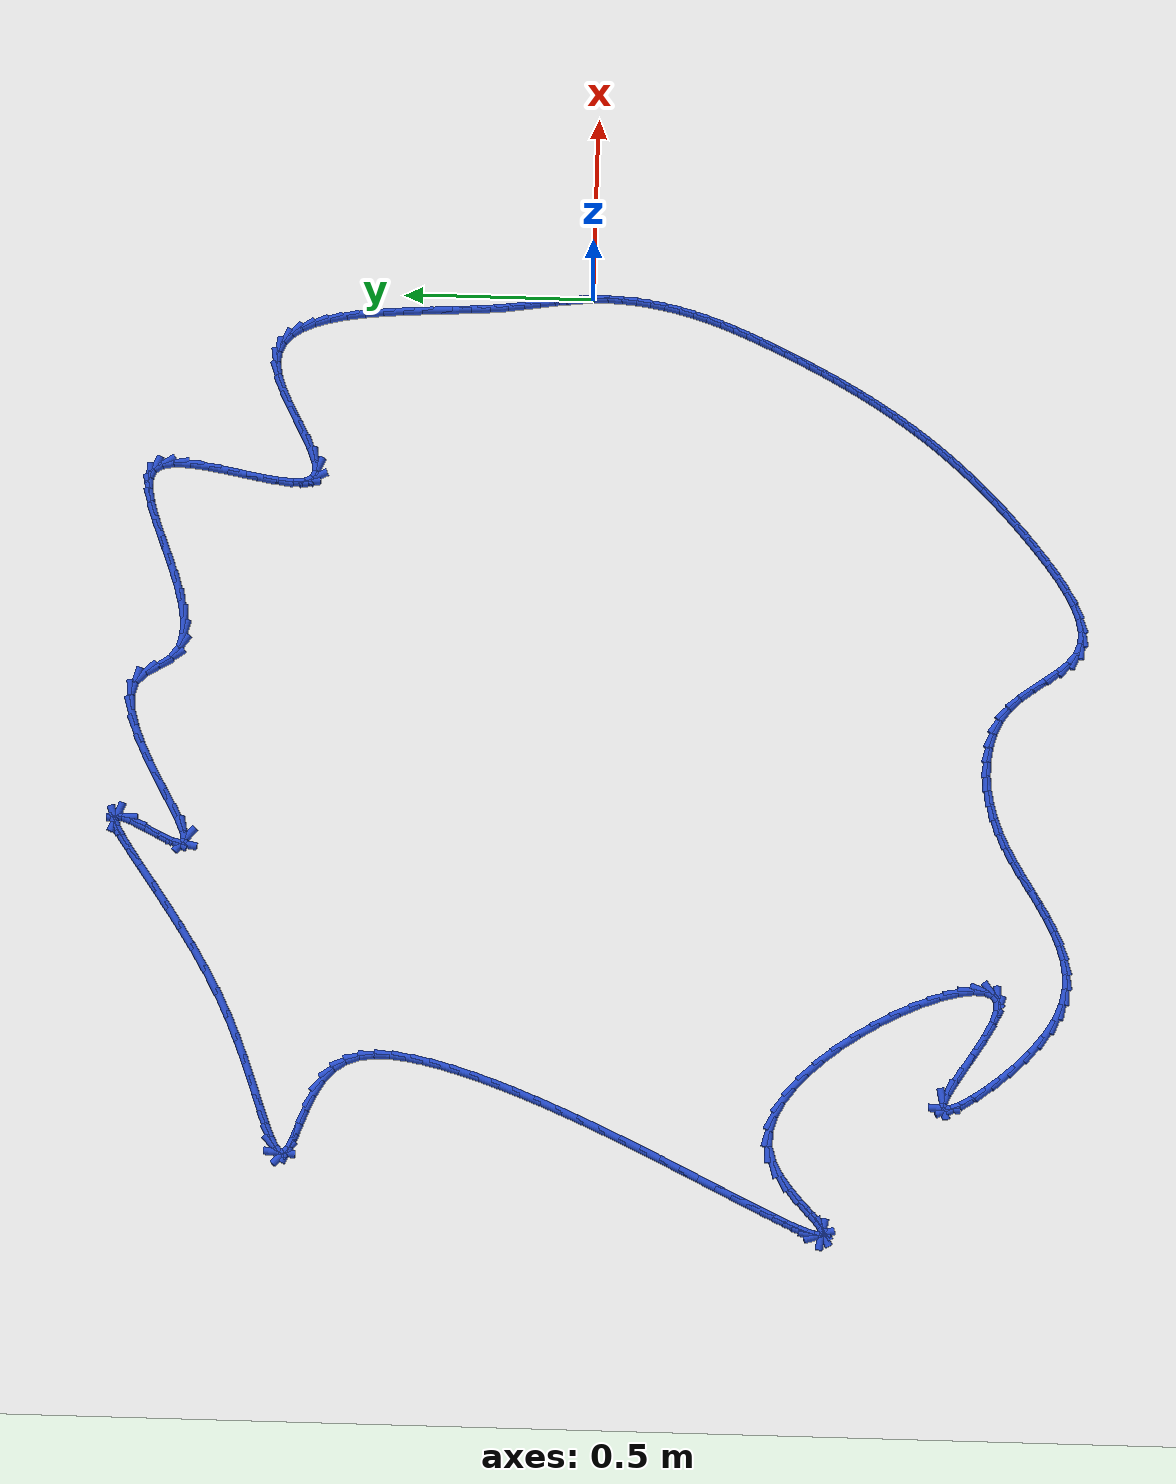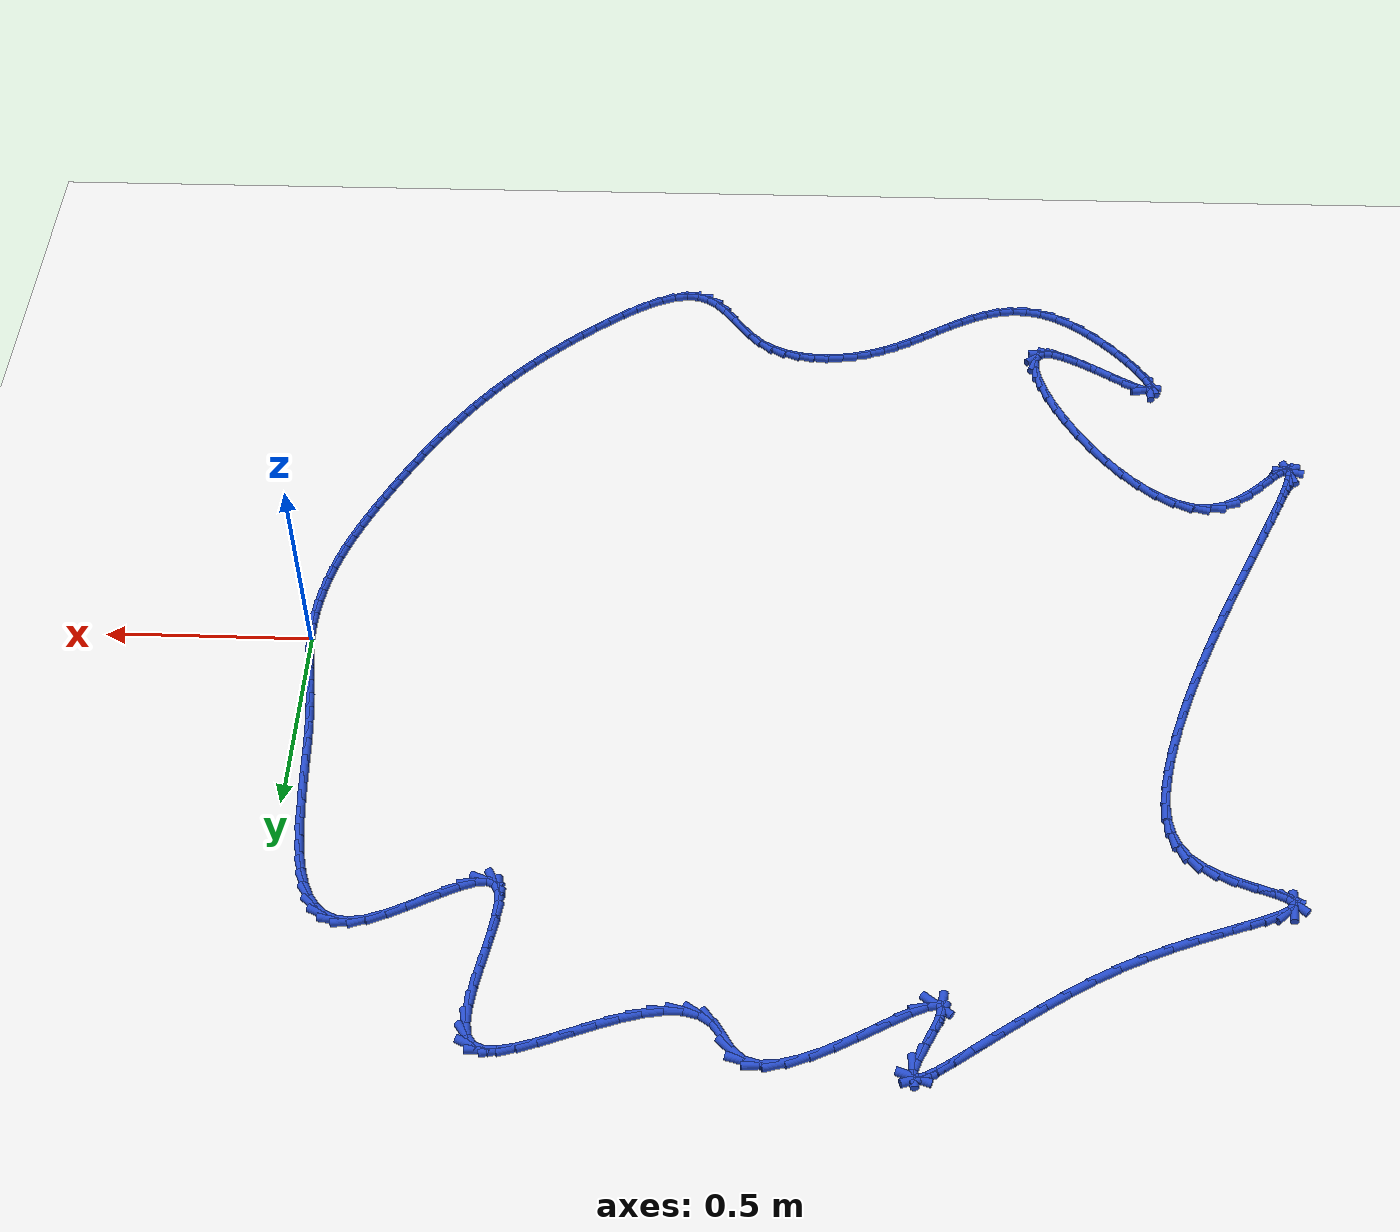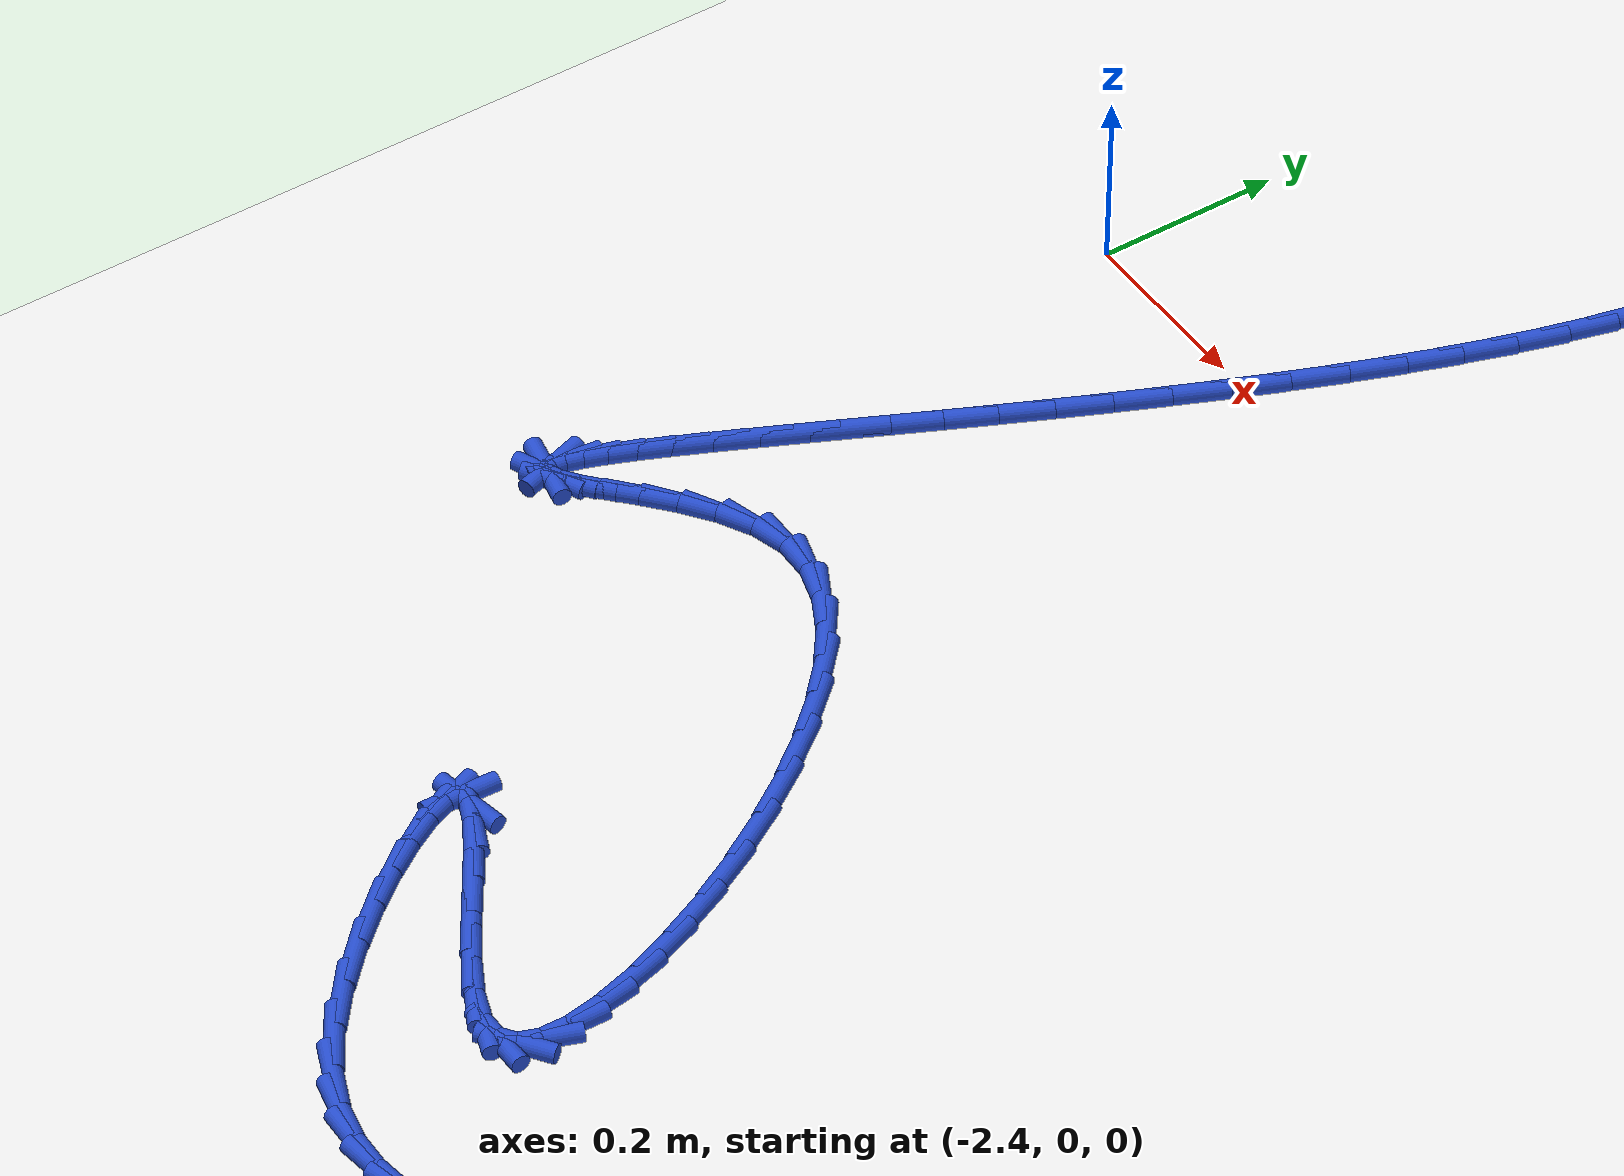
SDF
<sdf version="1.6">
 <world name="default">
  <light name="sun" type="directional">
   <pose>0 0 10 0 -0 0</pose>
   <diffuse>0.8 0.8 0.8 1</diffuse>
   <specular>0.2 0.2 0.2 1</specular>
   <attenuation>
    <range>1000</range>
    <constant>0.9</constant>
    <linear>0.01</linear>
    <quadratic>0.001</quadratic>
   </attenuation>
   <direction>-0.5 0.1 -0.9</direction>
  </light>
  <model name="ground_plane">
   <static>1</static>
   <link name="link">
    <collision name="collision">
     <geometry><plane><normal>0 0 1</normal><size>100 100</size></plane></geometry>
     <surface><friction><ode><mu>100</mu><mu2>50</mu2></ode></friction></surface>
    </collision>
    <visual name="visual">
     <cast_shadows>0</cast_shadows>
     <geometry><plane><normal>0 0 1</normal><size>100 100</size></plane></geometry>
     <material>
      <script><uri>file://media/materials/scripts/gazebo.material</uri><name>Gazebo/WhiteGlow</name></script>
     </material>
    </visual>
   </link>
  </model>
  <gravity>0 0 -9.8</gravity>
  <magnetic_field>6e-06 2.3e-05 -4.2e-05</magnetic_field>
  <atmosphere type="adiabatic"/>
  <physics name="default_physics" default="0" type="ode">
   <max_step_size>0.001</max_step_size>
   <real_time_factor>1</real_time_factor>
   <real_time_update_rate>1000</real_time_update_rate>
  </physics>
  <scene><ambient>0.4 0.4 0.4 1</ambient><background>0.7 0.7 0.7 1</background><shadows>1</shadows></scene>
  <spherical_coordinates>
   <surface_model>EARTH_WGS84</surface_model>
   <latitude_deg>0</latitude_deg>
   <longitude_deg>0</longitude_deg>
   <elevation>0</elevation>
   <heading_deg>0</heading_deg>
  </spherical_coordinates>
  <model name="line">
   <link name="link_0">
    <pose>-6.938893903907228e-18 1.3877787807814457e-17 0.01 0 1.57 -1.5029490095891989</pose>
    <collision name="collision">
     <geometry><cylinder><radius>0.01</radius><length>0.08</length></cylinder></geometry>
    </collision>
    <visual name="visual">
     <material>
      <script><name>Gazebo/Blue</name><uri>file://media/materials/scripts/gazebo.material</uri></script>
     </material>
     <geometry><cylinder><radius>0.01</radius><length>0.08</length></cylinder></geometry>
    </visual>
   </link>
   <link name="link_1">
    <pose>-0.0024324294258575665 0.035796491488146266 0.01 0 1.57 -1.4581747163771437</pose>
    <collision name="collision">
     <geometry><cylinder><radius>0.01</radius><length>0.08</length></cylinder></geometry>
    </collision>
    <visual name="visual">
     <material>
      <script><name>Gazebo/Blue</name><uri>file://media/materials/scripts/gazebo.material</uri></script>
     </material>
     <geometry><cylinder><radius>0.01</radius><length>0.08</length></cylinder></geometry>
    </visual>
   </link>
   <link name="link_2">
    <pose>-0.006441925883441868 0.07124732937667558 0.01 0 1.57 -1.4291554986315413</pose>
    <collision name="collision">
     <geometry><cylinder><radius>0.01</radius><length>0.08</length></cylinder></geometry>
    </collision>
    <visual name="visual">
     <material>
      <script><name>Gazebo/Blue</name><uri>file://media/materials/scripts/gazebo.material</uri></script>
     </material>
     <geometry><cylinder><radius>0.01</radius><length>0.08</length></cylinder></geometry>
    </visual>
   </link>
   <link name="link_3">
    <pose>-0.01154123499219159 0.10700793941399644 0.01 0 1.57 -1.4167709639370885</pose>
    <collision name="collision">
     <geometry><cylinder><radius>0.01</radius><length>0.08</length></cylinder></geometry>
    </collision>
    <visual name="visual">
     <material>
      <script><name>Gazebo/Blue</name><uri>file://media/materials/scripts/gazebo.material</uri></script>
     </material>
     <geometry><cylinder><radius>0.01</radius><length>0.08</length></cylinder></geometry>
    </visual>
   </link>
   <link name="link_4">
    <pose>-0.01724310237154544 0.14373374734851743 0.01 0 1.57 -1.420243754941917</pose>
    <collision name="collision">
     <geometry><cylinder><radius>0.01</radius><length>0.08</length></cylinder></geometry>
    </collision>
    <visual name="visual">
     <material>
      <script><name>Gazebo/Blue</name><uri>file://media/materials/scripts/gazebo.material</uri></script>
     </material>
     <geometry><cylinder><radius>0.01</radius><length>0.08</length></cylinder></geometry>
    </visual>
   </link>
   <link name="link_5">
    <pose>-0.0230602736409421 0.18208017892864706 0.01 0 1.57 -1.4375460999784744</pose>
    <collision name="collision">
     <geometry><cylinder><radius>0.01</radius><length>0.08</length></cylinder></geometry>
    </collision>
    <visual name="visual">
     <material>
      <script><name>Gazebo/Blue</name><uri>file://media/materials/scripts/gazebo.material</uri></script>
     </material>
     <geometry><cylinder><radius>0.01</radius><length>0.08</length></cylinder></geometry>
    </visual>
   </link>
   <link name="link_6">
    <pose>-0.028505494419820247 0.22270265990279367 0.01 0 1.57 -1.4656498363338808</pose>
    <collision name="collision">
     <geometry><cylinder><radius>0.01</radius><length>0.08</length></cylinder></geometry>
    </collision>
    <visual name="visual">
     <material>
      <script><name>Gazebo/Blue</name><uri>file://media/materials/scripts/gazebo.material</uri></script>
     </material>
     <geometry><cylinder><radius>0.01</radius><length>0.08</length></cylinder></geometry>
    </visual>
   </link>
   <link name="link_7">
    <pose>-0.03310041205159639 0.2662416467459656 0.01 0 1.57 -1.493004079329774</pose>
    <collision name="collision">
     <geometry><cylinder><radius>0.01</radius><length>0.08</length></cylinder></geometry>
    </collision>
    <visual name="visual">
     <material>
      <script><name>Gazebo/Blue</name><uri>file://media/materials/scripts/gazebo.material</uri></script>
     </material>
     <geometry><cylinder><radius>0.01</radius><length>0.08</length></cylinder></geometry>
    </visual>
   </link>
   <link name="link_8">
    <pose>-0.0367246024848403 0.31273569778830096 0.01 0 1.57 -1.5091628321506347</pose>
    <collision name="collision">
     <geometry><cylinder><radius>0.01</radius><length>0.08</length></cylinder></geometry>
    </collision>
    <visual name="visual">
     <material>
      <script><name>Gazebo/Blue</name><uri>file://media/materials/scripts/gazebo.material</uri></script>
     </material>
     <geometry><cylinder><radius>0.01</radius><length>0.08</length></cylinder></geometry>
    </visual>
   </link>
   <link name="link_9">
    <pose>-0.0397295919868771 0.36142973258047373 0.01 0 1.57 -1.5155548807561852</pose>
    <collision name="collision">
     <geometry><cylinder><radius>0.01</radius><length>0.08</length></cylinder></geometry>
    </collision>
    <visual name="visual">
     <material>
      <script><name>Gazebo/Blue</name><uri>file://media/materials/scripts/gazebo.material</uri></script>
     </material>
     <geometry><cylinder><radius>0.01</radius><length>0.08</length></cylinder></geometry>
    </visual>
   </link>
   <link name="link_10">
    <pose>-0.042499160980004204 0.41151443159932294 0.01 0 1.57 -1.513268462693427</pose>
    <collision name="collision">
     <geometry><cylinder><radius>0.01</radius><length>0.08</length></cylinder></geometry>
    </collision>
    <visual name="visual">
     <material>
      <script><name>Gazebo/Blue</name><uri>file://media/materials/scripts/gazebo.material</uri></script>
     </material>
     <geometry><cylinder><radius>0.01</radius><length>0.08</length></cylinder></geometry>
    </visual>
   </link>
   <link name="link_11">
    <pose>-0.045417089886519005 0.4621804753216886 0.01 0 1.57 -1.5025006209556657</pose>
    <collision name="collision">
     <geometry><cylinder><radius>0.01</radius><length>0.08</length></cylinder></geometry>
    </collision>
    <visual name="visual">
     <material>
      <script><name>Gazebo/Blue</name><uri>file://media/materials/scripts/gazebo.material</uri></script>
     </material>
     <geometry><cylinder><radius>0.01</radius><length>0.08</length></cylinder></geometry>
    </visual>
   </link>
   <link name="link_12">
    <pose>-0.04886715912871897 0.5126185442244102 0.01 0 1.57 -1.4826463805374432</pose>
    <collision name="collision">
     <geometry><cylinder><radius>0.01</radius><length>0.08</length></cylinder></geometry>
    </collision>
    <visual name="visual">
     <material>
      <script><name>Gazebo/Blue</name><uri>file://media/materials/scripts/gazebo.material</uri></script>
     </material>
     <geometry><cylinder><radius>0.01</radius><length>0.08</length></cylinder></geometry>
    </visual>
   </link>
   <link name="link_13">
    <pose>-0.05323314912890154 0.5620193187843275 0.01 0 1.57 -1.452213444151717</pose>
    <collision name="collision">
     <geometry><cylinder><radius>0.01</radius><length>0.08</length></cylinder></geometry>
    </collision>
    <visual name="visual">
     <material>
      <script><name>Gazebo/Blue</name><uri>file://media/materials/scripts/gazebo.material</uri></script>
     </material>
     <geometry><cylinder><radius>0.01</radius><length>0.08</length></cylinder></geometry>
    </visual>
   </link>
   <link name="link_14">
    <pose>-0.05889884030936408 0.6095734794782794 0.01 0 1.57 -1.4085499858642958</pose>
    <collision name="collision">
     <geometry><cylinder><radius>0.01</radius><length>0.08</length></cylinder></geometry>
    </collision>
    <visual name="visual">
     <material>
      <script><name>Gazebo/Blue</name><uri>file://media/materials/scripts/gazebo.material</uri></script>
     </material>
     <geometry><cylinder><radius>0.01</radius><length>0.08</length></cylinder></geometry>
    </visual>
   </link>
   <link name="link_15">
    <pose>-0.0662480130924041 0.6544717067831065 0.01 0 1.57 -1.347323174603074</pose>
    <collision name="collision">
     <geometry><cylinder><radius>0.01</radius><length>0.08</length></cylinder></geometry>
    </collision>
    <visual name="visual">
     <material>
      <script><name>Gazebo/Blue</name><uri>file://media/materials/scripts/gazebo.material</uri></script>
     </material>
     <geometry><cylinder><radius>0.01</radius><length>0.08</length></cylinder></geometry>
    </visual>
   </link>
   <link name="link_16">
    <pose>-0.075664447900319 0.6959046811756477 0.01 0 1.57 -1.2616601214778005</pose>
    <collision name="collision">
     <geometry><cylinder><radius>0.01</radius><length>0.08</length></cylinder></geometry>
    </collision>
    <visual name="visual">
     <material>
      <script><name>Gazebo/Blue</name><uri>file://media/materials/scripts/gazebo.material</uri></script>
     </material>
     <geometry><cylinder><radius>0.01</radius><length>0.08</length></cylinder></geometry>
    </visual>
   </link>
   <link name="link_17">
    <pose>-0.08753192515540617 0.7330630831327426 0.01 0 1.57 -1.1409958378339469</pose>
    <collision name="collision">
     <geometry><cylinder><radius>0.01</radius><length>0.08</length></cylinder></geometry>
    </collision>
    <visual name="visual">
     <material>
      <script><name>Gazebo/Blue</name><uri>file://media/materials/scripts/gazebo.material</uri></script>
     </material>
     <geometry><cylinder><radius>0.01</radius><length>0.08</length></cylinder></geometry>
    </visual>
   </link>
   <link name="link_18">
    <pose>-0.10223422527996309 0.7651375931312314 0.01 0 1.57 -0.9705540528261299</pose>
    <collision name="collision">
     <geometry><cylinder><radius>0.01</radius><length>0.08</length></cylinder></geometry>
    </collision>
    <visual name="visual">
     <material>
      <script><name>Gazebo/Blue</name><uri>file://media/materials/scripts/gazebo.material</uri></script>
     </material>
     <geometry><cylinder><radius>0.01</radius><length>0.08</length></cylinder></geometry>
    </visual>
   </link>
   <link name="link_19">
    <pose>-0.12015512869628711 0.7913188916479525 0.01 0 1.57 -0.7355755957059619</pose>
    <collision name="collision">
     <geometry><cylinder><radius>0.01</radius><length>0.08</length></cylinder></geometry>
    </collision>
    <visual name="visual">
     <material>
      <script><name>Gazebo/Blue</name><uri>file://media/materials/scripts/gazebo.material</uri></script>
     </material>
     <geometry><cylinder><radius>0.01</radius><length>0.08</length></cylinder></geometry>
    </visual>
   </link>
   <link name="link_20">
    <pose>-0.14167841582667579 0.8107976591597468 0.01 0 1.57 -0.4386373959741869</pose>
    <collision name="collision">
     <geometry><cylinder><radius>0.01</radius><length>0.08</length></cylinder></geometry>
    </collision>
    <visual name="visual">
     <material>
      <script><name>Gazebo/Blue</name><uri>file://media/materials/scripts/gazebo.material</uri></script>
     </material>
     <geometry><cylinder><radius>0.01</radius><length>0.08</length></cylinder></geometry>
    </visual>
   </link>
   <link name="link_21">
    <pose>-0.16718786709342648 0.8227645761434532 0.01 0 1.57 -0.12141525651706091</pose>
    <collision name="collision">
     <geometry><cylinder><radius>0.01</radius><length>0.08</length></cylinder></geometry>
    </collision>
    <visual name="visual">
     <material>
      <script><name>Gazebo/Blue</name><uri>file://media/materials/scripts/gazebo.material</uri></script>
     </material>
     <geometry><cylinder><radius>0.01</radius><length>0.08</length></cylinder></geometry>
    </visual>
   </link>
   <link name="link_22">
    <pose>-0.19706726291883653 0.8264103230759113 0.01 0 1.57 0.15551919759422433</pose>
    <collision name="collision">
     <geometry><cylinder><radius>0.01</radius><length>0.08</length></cylinder></geometry>
    </collision>
    <visual name="visual">
     <material>
      <script><name>Gazebo/Blue</name><uri>file://media/materials/scripts/gazebo.material</uri></script>
     </material>
     <geometry><cylinder><radius>0.01</radius><length>0.08</length></cylinder></geometry>
    </visual>
   </link>
   <link name="link_23">
    <pose>-0.23166478676584346 0.820985941488289 0.01 0 1.57 0.33773264753974835</pose>
    <collision name="collision">
     <geometry><cylinder><radius>0.01</radius><length>0.08</length></cylinder></geometry>
    </collision>
    <visual name="visual">
     <material>
      <script><name>Gazebo/Blue</name><uri>file://media/materials/scripts/gazebo.material</uri></script>
     </material>
     <geometry><cylinder><radius>0.01</radius><length>0.08</length></cylinder></geometry>
    </visual>
   </link>
   <link name="link_24">
    <pose>-0.2703512929469173 0.8073997104682087 0.01 0 1.57 0.43364230961249856</pose>
    <collision name="collision">
     <geometry><cylinder><radius>0.01</radius><length>0.08</length></cylinder></geometry>
    </collision>
    <visual name="visual">
     <material>
      <script><name>Gazebo/Blue</name><uri>file://media/materials/scripts/gazebo.material</uri></script>
     </material>
     <geometry><cylinder><radius>0.01</radius><length>0.08</length></cylinder></geometry>
    </visual>
   </link>
   <link name="link_25">
    <pose>-0.3114231217208325 0.7883819411626845 0.01 0 1.57 0.4784316106165716</pose>
    <collision name="collision">
     <geometry><cylinder><radius>0.01</radius><length>0.08</length></cylinder></geometry>
    </collision>
    <visual name="visual">
     <material>
      <script><name>Gazebo/Blue</name><uri>file://media/materials/scripts/gazebo.material</uri></script>
     </material>
     <geometry><cylinder><radius>0.01</radius><length>0.08</length></cylinder></geometry>
    </visual>
   </link>
   <link name="link_26">
    <pose>-0.3531215246306627 0.7667563575556949 0.01 0 1.57 0.4856166937264182</pose>
    <collision name="collision">
     <geometry><cylinder><radius>0.01</radius><length>0.08</length></cylinder></geometry>
    </collision>
    <visual name="visual">
     <material>
      <script><name>Gazebo/Blue</name><uri>file://media/materials/scripts/gazebo.material</uri></script>
     </material>
     <geometry><cylinder><radius>0.01</radius><length>0.08</length></cylinder></geometry>
    </visual>
   </link>
   <link name="link_27">
    <pose>-0.39368775321948135 0.7453466836312201 0.01 0 1.57 0.4536690798772381</pose>
    <collision name="collision">
     <geometry><cylinder><radius>0.01</radius><length>0.08</length></cylinder></geometry>
    </collision>
    <visual name="visual">
     <material>
      <script><name>Gazebo/Blue</name><uri>file://media/materials/scripts/gazebo.material</uri></script>
     </material>
     <geometry><cylinder><radius>0.01</radius><length>0.08</length></cylinder></geometry>
    </visual>
   </link>
   <link name="link_28">
    <pose>-0.43136305903036304 0.7269766433732396 0.01 0 1.57 0.3620072377387617</pose>
    <collision name="collision">
     <geometry><cylinder><radius>0.01</radius><length>0.08</length></cylinder></geometry>
    </collision>
    <visual name="visual">
     <material>
      <script><name>Gazebo/Blue</name><uri>file://media/materials/scripts/gazebo.material</uri></script>
     </material>
     <geometry><cylinder><radius>0.01</radius><length>0.08</length></cylinder></geometry>
    </visual>
   </link>
   <link name="link_29">
    <pose>-0.46438869360638063 0.7144699607657328 0.01 0 1.57 0.14252812563000053</pose>
    <collision name="collision">
     <geometry><cylinder><radius>0.01</radius><length>0.08</length></cylinder></geometry>
    </collision>
    <visual name="visual">
     <material>
      <script><name>Gazebo/Blue</name><uri>file://media/materials/scripts/gazebo.material</uri></script>
     </material>
     <geometry><cylinder><radius>0.01</radius><length>0.08</length></cylinder></geometry>
    </visual>
   </link>
   <link name="link_30">
    <pose>-0.49100590849060816 0.7106503597926793 0.01 0 1.57 -0.3937129141649056</pose>
    <collision name="collision">
     <geometry><cylinder><radius>0.01</radius><length>0.08</length></cylinder></geometry>
    </collision>
    <visual name="visual">
     <material>
      <script><name>Gazebo/Blue</name><uri>file://media/materials/scripts/gazebo.material</uri></script>
     </material>
     <geometry><cylinder><radius>0.01</radius><length>0.08</length></cylinder></geometry>
    </visual>
   </link>
   <link name="link_31">
    <pose>-0.5094701226348705 0.7183204283298726 0.01 0 1.57 -1.1211510820049249</pose>
    <collision name="collision">
     <geometry><cylinder><radius>0.01</radius><length>0.08</length></cylinder></geometry>
    </collision>
    <visual name="visual">
     <material>
      <script><name>Gazebo/Blue</name><uri>file://media/materials/scripts/gazebo.material</uri></script>
     </material>
     <geometry><cylinder><radius>0.01</radius><length>0.08</length></cylinder></geometry>
    </visual>
   </link>
   <link name="link_32">
    <pose>-0.5192185936477617 0.7385195899265792 0.01 0 1.57 -1.4887960989691764</pose>
    <collision name="collision">
     <geometry><cylinder><radius>0.01</radius><length>0.08</length></cylinder></geometry>
    </collision>
    <visual name="visual">
     <material>
      <script><name>Gazebo/Blue</name><uri>file://media/materials/scripts/gazebo.material</uri></script>
     </material>
     <geometry><cylinder><radius>0.01</radius><length>0.08</length></cylinder></geometry>
    </visual>
   </link>
   <link name="link_33">
    <pose>-0.521742004190373 0.7692237993759778 0.01 0 1.57 1.4936423378329293</pose>
    <collision name="collision">
     <geometry><cylinder><radius>0.01</radius><length>0.08</length></cylinder></geometry>
    </collision>
    <visual name="visual">
     <material>
      <script><name>Gazebo/Blue</name><uri>file://media/materials/scripts/gazebo.material</uri></script>
     </material>
     <geometry><cylinder><radius>0.01</radius><length>0.08</length></cylinder></geometry>
    </visual>
   </link>
   <link name="link_34">
    <pose>-0.518736378246912 0.8081026663592397 0.01 0 1.57 1.4190611112322715</pose>
    <collision name="collision">
     <geometry><cylinder><radius>0.01</radius><length>0.08</length></cylinder></geometry>
    </collision>
    <visual name="visual">
     <material>
      <script><name>Gazebo/Blue</name><uri>file://media/materials/scripts/gazebo.material</uri></script>
     </material>
     <geometry><cylinder><radius>0.01</radius><length>0.08</length></cylinder></geometry>
    </visual>
   </link>
   <link name="link_35">
    <pose>-0.5118977398015865 0.8528258005575355 0.01 0 1.57 1.38682683542851</pose>
    <collision name="collision">
     <geometry><cylinder><radius>0.01</radius><length>0.08</length></cylinder></geometry>
    </collision>
    <visual name="visual">
     <material>
      <script><name>Gazebo/Blue</name><uri>file://media/materials/scripts/gazebo.material</uri></script>
     </material>
     <geometry><cylinder><radius>0.01</radius><length>0.08</length></cylinder></geometry>
    </visual>
   </link>
   <link name="link_36">
    <pose>-0.502922112838605 0.9010628116520373 0.01 0 1.57 1.3825130540014907</pose>
    <collision name="collision">
     <geometry><cylinder><radius>0.01</radius><length>0.08</length></cylinder></geometry>
    </collision>
    <visual name="visual">
     <material>
      <script><name>Gazebo/Blue</name><uri>file://media/materials/scripts/gazebo.material</uri></script>
     </material>
     <geometry><cylinder><radius>0.01</radius><length>0.08</length></cylinder></geometry>
    </visual>
   </link>
   <link name="link_37">
    <pose>-0.4935055213421753 0.9504833093239153 0.01 0 1.57 1.4033118876343589</pose>
    <collision name="collision">
     <geometry><cylinder><radius>0.01</radius><length>0.08</length></cylinder></geometry>
    </collision>
    <visual name="visual">
     <material>
      <script><name>Gazebo/Blue</name><uri>file://media/materials/scripts/gazebo.material</uri></script>
     </material>
     <geometry><cylinder><radius>0.01</radius><length>0.08</length></cylinder></geometry>
    </visual>
   </link>
   <link name="link_38">
    <pose>-0.48534398929650524 0.9987569032543417 0.01 0 1.57 1.455002385339137</pose>
    <collision name="collision">
     <geometry><cylinder><radius>0.01</radius><length>0.08</length></cylinder></geometry>
    </collision>
    <visual name="visual">
     <material>
      <script><name>Gazebo/Blue</name><uri>file://media/materials/scripts/gazebo.material</uri></script>
     </material>
     <geometry><cylinder><radius>0.01</radius><length>0.08</length></cylinder></geometry>
    </visual>
   </link>
   <link name="link_39">
    <pose>-0.48013354068580283 1.0435532031244874 0.01 0 1.57 1.5563484684523539</pose>
    <collision name="collision">
     <geometry><cylinder><radius>0.01</radius><length>0.08</length></cylinder></geometry>
    </collision>
    <visual name="visual">
     <material>
      <script><name>Gazebo/Blue</name><uri>file://media/materials/scripts/gazebo.material</uri></script>
     </material>
     <geometry><cylinder><radius>0.01</radius><length>0.08</length></cylinder></geometry>
    </visual>
   </link>
   <link name="link_40">
    <pose>-0.4795701994942762 1.0825418186155233 0.01 0 1.57 -1.385595121645287</pose>
    <collision name="collision">
     <geometry><cylinder><radius>0.01</radius><length>0.08</length></cylinder></geometry>
    </collision>
    <visual name="visual">
     <material>
      <script><name>Gazebo/Blue</name><uri>file://media/materials/scripts/gazebo.material</uri></script>
     </material>
     <geometry><cylinder><radius>0.01</radius><length>0.08</length></cylinder></geometry>
    </visual>
   </link>
   <link name="link_41">
    <pose>-0.48534998970613336 1.113392359408621 0.01 0 1.57 -0.9777811911724729</pose>
    <collision name="collision">
     <geometry><cylinder><radius>0.01</radius><length>0.08</length></cylinder></geometry>
    </collision>
    <visual name="visual">
     <material>
      <script><name>Gazebo/Blue</name><uri>file://media/materials/scripts/gazebo.material</uri></script>
     </material>
     <geometry><cylinder><radius>0.01</radius><length>0.08</length></cylinder></geometry>
    </visual>
   </link>
   <link name="link_42">
    <pose>-0.49912662661353785 1.1338345563181706 0.01 0 1.57 -0.4091905115053014</pose>
    <collision name="collision">
     <geometry><cylinder><radius>0.01</radius><length>0.08</length></cylinder></geometry>
    </collision>
    <visual name="visual">
     <material>
      <script><name>Gazebo/Blue</name><uri>file://media/materials/scripts/gazebo.material</uri></script>
     </material>
     <geometry><cylinder><radius>0.01</radius><length>0.08</length></cylinder></geometry>
    </visual>
   </link>
   <link name="link_43">
    <pose>-0.5212619214378263 1.1434339505557993 0.01 0 1.57 -0.015383986659590978</pose>
    <collision name="collision">
     <geometry><cylinder><radius>0.01</radius><length>0.08</length></cylinder></geometry>
    </collision>
    <visual name="visual">
     <material>
      <script><name>Gazebo/Blue</name><uri>file://media/materials/scripts/gazebo.material</uri></script>
     </material>
     <geometry><cylinder><radius>0.01</radius><length>0.08</length></cylinder></geometry>
    </visual>
   </link>
   <link name="link_44">
    <pose>-0.5506190816360831 1.1438856163486846 0.01 0 1.57 0.19222493038312605</pose>
    <collision name="collision">
     <geometry><cylinder><radius>0.01</radius><length>0.08</length></cylinder></geometry>
    </collision>
    <visual name="visual">
     <material>
      <script><name>Gazebo/Blue</name><uri>file://media/materials/scripts/gazebo.material</uri></script>
     </material>
     <geometry><cylinder><radius>0.01</radius><length>0.08</length></cylinder></geometry>
    </visual>
   </link>
   <link name="link_45">
    <pose>-0.5859773803668158 1.1370038995181515 0.01 0 1.57 0.29964514804853004</pose>
    <collision name="collision">
     <geometry><cylinder><radius>0.01</radius><length>0.08</length></cylinder></geometry>
    </collision>
    <visual name="visual">
     <material>
      <script><name>Gazebo/Blue</name><uri>file://media/materials/scripts/gazebo.material</uri></script>
     </material>
     <geometry><cylinder><radius>0.01</radius><length>0.08</length></cylinder></geometry>
    </visual>
   </link>
   <link name="link_46">
    <pose>-0.6261160907885323 1.1246031458855246 0.01 0 1.57 0.35311199952206024</pose>
    <collision name="collision">
     <geometry><cylinder><radius>0.01</radius><length>0.08</length></cylinder></geometry>
    </collision>
    <visual name="visual">
     <material>
      <script><name>Gazebo/Blue</name><uri>file://media/materials/scripts/gazebo.material</uri></script>
     </material>
     <geometry><cylinder><radius>0.01</radius><length>0.08</length></cylinder></geometry>
    </visual>
   </link>
   <link name="link_47">
    <pose>-0.6698144860597397 1.1084977012721287 0.01 0 1.57 0.37263303045988466</pose>
    <collision name="collision">
     <geometry><cylinder><radius>0.01</radius><length>0.08</length></cylinder></geometry>
    </collision>
    <visual name="visual">
     <material>
      <script><name>Gazebo/Blue</name><uri>file://media/materials/scripts/gazebo.material</uri></script>
     </material>
     <geometry><cylinder><radius>0.01</radius><length>0.08</length></cylinder></geometry>
    </visual>
   </link>
   <link name="link_48">
    <pose>-0.7158518393389465 1.0905019114992887 0.01 0 1.57 0.3659729729368808</pose>
    <collision name="collision">
     <geometry><cylinder><radius>0.01</radius><length>0.08</length></cylinder></geometry>
    </collision>
    <visual name="visual">
     <material>
      <script><name>Gazebo/Blue</name><uri>file://media/materials/scripts/gazebo.material</uri></script>
     </material>
     <geometry><cylinder><radius>0.01</radius><length>0.08</length></cylinder></geometry>
    </visual>
   </link>
   <link name="link_49">
    <pose>-0.7630074237846595 1.0724301223883286 0.01 0 1.57 0.33411391972943194</pose>
    <collision name="collision">
     <geometry><cylinder><radius>0.01</radius><length>0.08</length></cylinder></geometry>
    </collision>
    <visual name="visual">
     <material>
      <script><name>Gazebo/Blue</name><uri>file://media/materials/scripts/gazebo.material</uri></script>
     </material>
     <geometry><cylinder><radius>0.01</radius><length>0.08</length></cylinder></geometry>
    </visual>
   </link>
   <link name="link_50">
    <pose>-0.8100605125553867 1.0560966797605735 0.01 0 1.57 0.27252983559960847</pose>
    <collision name="collision">
     <geometry><cylinder><radius>0.01</radius><length>0.08</length></cylinder></geometry>
    </collision>
    <visual name="visual">
     <material>
      <script><name>Gazebo/Blue</name><uri>file://media/materials/scripts/gazebo.material</uri></script>
     </material>
     <geometry><cylinder><radius>0.01</radius><length>0.08</length></cylinder></geometry>
    </visual>
   </link>
   <link name="link_51">
    <pose>-0.855790378809636 1.0433159294373486 0.01 0 1.57 0.17001248220391646</pose>
    <collision name="collision">
     <geometry><cylinder><radius>0.01</radius><length>0.08</length></cylinder></geometry>
    </collision>
    <visual name="visual">
     <material>
      <script><name>Gazebo/Blue</name><uri>file://media/materials/scripts/gazebo.material</uri></script>
     </material>
     <geometry><cylinder><radius>0.01</radius><length>0.08</length></cylinder></geometry>
    </visual>
   </link>
   <link name="link_52">
    <pose>-0.8989762957059144 1.0359022172399777 0.01 0 1.57 0.0058934106668151656</pose>
    <collision name="collision">
     <geometry><cylinder><radius>0.01</radius><length>0.08</length></cylinder></geometry>
    </collision>
    <visual name="visual">
     <material>
      <script><name>Gazebo/Blue</name><uri>file://media/materials/scripts/gazebo.material</uri></script>
     </material>
     <geometry><cylinder><radius>0.01</radius><length>0.08</length></cylinder></geometry>
    </visual>
   </link>
   <link name="link_53">
    <pose>-0.9383975364027298 1.0356698889897857 0.01 0 1.57 -0.24919529305724566</pose>
    <collision name="collision">
     <geometry><cylinder><radius>0.01</radius><length>0.08</length></cylinder></geometry>
    </collision>
    <visual name="visual">
     <material>
      <script><name>Gazebo/Blue</name><uri>file://media/materials/scripts/gazebo.material</uri></script>
     </material>
     <geometry><cylinder><radius>0.01</radius><length>0.08</length></cylinder></geometry>
    </visual>
   </link>
   <link name="link_54">
    <pose>-0.9728333740585905 1.0444332905080982 0.01 0 1.57 -0.6062587097577087</pose>
    <collision name="collision">
     <geometry><cylinder><radius>0.01</radius><length>0.08</length></cylinder></geometry>
    </collision>
    <visual name="visual">
     <material>
      <script><name>Gazebo/Blue</name><uri>file://media/materials/scripts/gazebo.material</uri></script>
     </material>
     <geometry><cylinder><radius>0.01</radius><length>0.08</length></cylinder></geometry>
    </visual>
   </link>
   <link name="link_55">
    <pose>-1.0010630818320032 1.0640067676162384 0.01 0 1.57 -0.959277237569955</pose>
    <collision name="collision">
     <geometry><cylinder><radius>0.01</radius><length>0.08</length></cylinder></geometry>
    </collision>
    <visual name="visual">
     <material>
      <script><name>Gazebo/Blue</name><uri>file://media/materials/scripts/gazebo.material</uri></script>
     </material>
     <geometry><cylinder><radius>0.01</radius><length>0.08</length></cylinder></geometry>
    </visual>
   </link>
   <link name="link_56">
    <pose>-1.0226874596790703 1.0948466424547614 0.01 0 1.57 -1.034687938574385</pose>
    <collision name="collision">
     <geometry><cylinder><radius>0.01</radius><length>0.08</length></cylinder></geometry>
    </collision>
    <visual name="visual">
     <material>
      <script><name>Gazebo/Blue</name><uri>file://media/materials/scripts/gazebo.material</uri></script>
     </material>
     <geometry><cylinder><radius>0.01</radius><length>0.08</length></cylinder></geometry>
    </visual>
   </link>
   <link name="link_57">
    <pose>-1.042689714047884 1.1285118579222166 0.01 0 1.57 -0.7680621147179204</pose>
    <collision name="collision">
     <geometry><cylinder><radius>0.01</radius><length>0.08</length></cylinder></geometry>
    </collision>
    <visual name="visual">
     <material>
      <script><name>Gazebo/Blue</name><uri>file://media/materials/scripts/gazebo.material</uri></script>
     </material>
     <geometry><cylinder><radius>0.01</radius><length>0.08</length></cylinder></geometry>
    </visual>
   </link>
   <link name="link_58">
    <pose>-1.0681449423753462 1.1530994544807123 0.01 0 1.57 -0.2675079446141565</pose>
    <collision name="collision">
     <geometry><cylinder><radius>0.01</radius><length>0.08</length></cylinder></geometry>
    </collision>
    <visual name="visual">
     <material>
      <script><name>Gazebo/Blue</name><uri>file://media/materials/scripts/gazebo.material</uri></script>
     </material>
     <geometry><cylinder><radius>0.01</radius><length>0.08</length></cylinder></geometry>
    </visual>
   </link>
   <link name="link_59">
    <pose>-1.1024997097435514 1.1625153076003214 0.01 0 1.57 0.0852445513349359</pose>
    <collision name="collision">
     <geometry><cylinder><radius>0.01</radius><length>0.08</length></cylinder></geometry>
    </collision>
    <visual name="visual">
     <material>
      <script><name>Gazebo/Blue</name><uri>file://media/materials/scripts/gazebo.material</uri></script>
     </material>
     <geometry><cylinder><radius>0.01</radius><length>0.08</length></cylinder></geometry>
    </visual>
   </link>
   <link name="link_60">
    <pose>-1.1440146408572283 1.1589677889188155 0.01 0 1.57 0.2856217911963571</pose>
    <collision name="collision">
     <geometry><cylinder><radius>0.01</radius><length>0.08</length></cylinder></geometry>
    </collision>
    <visual name="visual">
     <material>
      <script><name>Gazebo/Blue</name><uri>file://media/materials/scripts/gazebo.material</uri></script>
     </material>
     <geometry><cylinder><radius>0.01</radius><length>0.08</length></cylinder></geometry>
    </visual>
   </link>
   <link name="link_61">
    <pose>-1.1905527481908416 1.1453018323515494 0.01 0 1.57 0.400741339856995</pose>
    <collision name="collision">
     <geometry><cylinder><radius>0.01</radius><length>0.08</length></cylinder></geometry>
    </collision>
    <visual name="visual">
     <material>
      <script><name>Gazebo/Blue</name><uri>file://media/materials/scripts/gazebo.material</uri></script>
     </material>
     <geometry><cylinder><radius>0.01</radius><length>0.08</length></cylinder></geometry>
    </visual>
   </link>
   <link name="link_62">
    <pose>-1.2399770442188545 1.1243623718138767 0.01 0 1.57 0.46812249363446756</pose>
    <collision name="collision">
     <geometry><cylinder><radius>0.01</radius><length>0.08</length></cylinder></geometry>
    </collision>
    <visual name="visual">
     <material>
      <script><name>Gazebo/Blue</name><uri>file://media/materials/scripts/gazebo.material</uri></script>
     </material>
     <geometry><cylinder><radius>0.01</radius><length>0.08</length></cylinder></geometry>
    </visual>
   </link>
   <link name="link_63">
    <pose>-1.2901505414157304 1.098994341221151 0.01 0 1.57 0.5047222750536078</pose>
    <collision name="collision">
     <geometry><cylinder><radius>0.01</radius><length>0.08</length></cylinder></geometry>
    </collision>
    <visual name="visual">
     <material>
      <script><name>Gazebo/Blue</name><uri>file://media/materials/scripts/gazebo.material</uri></script>
     </material>
     <geometry><cylinder><radius>0.01</radius><length>0.08</length></cylinder></geometry>
    </visual>
   </link>
   <link name="link_64">
    <pose>-1.3389362522559334 1.072042674488726 0.01 0 1.57 0.5162595644142666</pose>
    <collision name="collision">
     <geometry><cylinder><radius>0.01</radius><length>0.08</length></cylinder></geometry>
    </collision>
    <visual name="visual">
     <material>
      <script><name>Gazebo/Blue</name><uri>file://media/materials/scripts/gazebo.material</uri></script>
     </material>
     <geometry><cylinder><radius>0.01</radius><length>0.08</length></cylinder></geometry>
    </visual>
   </link>
   <link name="link_65">
    <pose>-1.3841971892139258 1.0463523055319557 0.01 0 1.57 0.4990466957613119</pose>
    <collision name="collision">
     <geometry><cylinder><radius>0.01</radius><length>0.08</length></cylinder></geometry>
    </collision>
    <visual name="visual">
     <material>
      <script><name>Gazebo/Blue</name><uri>file://media/materials/scripts/gazebo.material</uri></script>
     </material>
     <geometry><cylinder><radius>0.01</radius><length>0.08</length></cylinder></geometry>
    </visual>
   </link>
   <link name="link_66">
    <pose>-1.4237963647641723 1.0247681682661935 0.01 0 1.57 0.43126267578423383</pose>
    <collision name="collision">
     <geometry><cylinder><radius>0.01</radius><length>0.08</length></cylinder></geometry>
    </collision>
    <visual name="visual">
     <material>
      <script><name>Gazebo/Blue</name><uri>file://media/materials/scripts/gazebo.material</uri></script>
     </material>
     <geometry><cylinder><radius>0.01</radius><length>0.08</length></cylinder></geometry>
    </visual>
   </link>
   <link name="link_67">
    <pose>-1.4555967913811358 1.0101351966067935 0.01 0 1.57 0.21771217513708524</pose>
    <collision name="collision">
     <geometry><cylinder><radius>0.01</radius><length>0.08</length></cylinder></geometry>
    </collision>
    <visual name="visual">
     <material>
      <script><name>Gazebo/Blue</name><uri>file://media/materials/scripts/gazebo.material</uri></script>
     </material>
     <geometry><cylinder><radius>0.01</radius><length>0.08</length></cylinder></geometry>
    </visual>
   </link>
   <link name="link_68">
    <pose>-1.4774614815392806 1.0052983244691098 0.01 0 1.57 -0.6729067629164983</pose>
    <collision name="collision">
     <geometry><cylinder><radius>0.01</radius><length>0.08</length></cylinder></geometry>
    </collision>
    <visual name="visual">
     <material>
      <script><name>Gazebo/Blue</name><uri>file://media/materials/scripts/gazebo.material</uri></script>
     </material>
     <geometry><cylinder><radius>0.01</radius><length>0.08</length></cylinder></geometry>
    </visual>
   </link>
   <link name="link_69">
    <pose>-1.4872534477130694 1.0131024857684958 0.01 0 1.57 1.392757686864441</pose>
    <collision name="collision">
     <geometry><cylinder><radius>0.01</radius><length>0.08</length></cylinder></geometry>
    </collision>
    <visual name="visual">
     <material>
      <script><name>Gazebo/Blue</name><uri>file://media/materials/scripts/gazebo.material</uri></script>
     </material>
     <geometry><cylinder><radius>0.01</radius><length>0.08</length></cylinder></geometry>
    </visual>
   </link>
   <link name="link_70">
    <pose>-1.483125310184112 1.036043727693861 0.01 0 1.57 1.1606052238844655</pose>
    <collision name="collision">
     <geometry><cylinder><radius>0.01</radius><length>0.08</length></cylinder></geometry>
    </collision>
    <visual name="visual">
     <material>
      <script><name>Gazebo/Blue</name><uri>file://media/materials/scripts/gazebo.material</uri></script>
     </material>
     <geometry><cylinder><radius>0.01</radius><length>0.08</length></cylinder></geometry>
    </visual>
   </link>
   <link name="link_71">
    <pose>-1.4679584525032106 1.070921418351538 0.01 0 1.57 1.1074564694223479</pose>
    <collision name="collision">
     <geometry><cylinder><radius>0.01</radius><length>0.08</length></cylinder></geometry>
    </collision>
    <visual name="visual">
     <material>
      <script><name>Gazebo/Blue</name><uri>file://media/materials/scripts/gazebo.material</uri></script>
     </material>
     <geometry><cylinder><radius>0.01</radius><length>0.08</length></cylinder></geometry>
    </visual>
   </link>
   <link name="link_72">
    <pose>-1.4484879102108912 1.1098924818447067 0.01 0 1.57 1.1212957878696206</pose>
    <collision name="collision">
     <geometry><cylinder><radius>0.01</radius><length>0.08</length></cylinder></geometry>
    </collision>
    <visual name="visual">
     <material>
      <script><name>Gazebo/Blue</name><uri>file://media/materials/scripts/gazebo.material</uri></script>
     </material>
     <geometry><cylinder><radius>0.01</radius><length>0.08</length></cylinder></geometry>
    </visual>
   </link>
   <link name="link_73">
    <pose>-1.4315610035052702 1.1449785744224015 0.01 0 1.57 1.2330762547042402</pose>
    <collision name="collision">
     <geometry><cylinder><radius>0.01</radius><length>0.08</length></cylinder></geometry>
    </collision>
    <visual name="visual">
     <material>
      <script><name>Gazebo/Blue</name><uri>file://media/materials/scripts/gazebo.material</uri></script>
     </material>
     <geometry><cylinder><radius>0.01</radius><length>0.08</length></cylinder></geometry>
    </visual>
   </link>
   <link name="link_74">
    <pose>-1.4229451271656062 1.1695130874061914 0.01 0 1.57 -1.5355318231440795</pose>
    <collision name="collision">
     <geometry><cylinder><radius>0.01</radius><length>0.08</length></cylinder></geometry>
    </collision>
    <visual name="visual">
     <material>
      <script><name>Gazebo/Blue</name><uri>file://media/materials/scripts/gazebo.material</uri></script>
     </material>
     <geometry><cylinder><radius>0.01</radius><length>0.08</length></cylinder></geometry>
    </visual>
   </link>
   <link name="link_75">
    <pose>-1.4234170966059778 1.1828912362688928 0.01 0 1.57 -0.3618077404431063</pose>
    <collision name="collision">
     <geometry><cylinder><radius>0.01</radius><length>0.08</length></cylinder></geometry>
    </collision>
    <visual name="visual">
     <material>
      <script><name>Gazebo/Blue</name><uri>file://media/materials/scripts/gazebo.material</uri></script>
     </material>
     <geometry><cylinder><radius>0.01</radius><length>0.08</length></cylinder></geometry>
    </visual>
   </link>
   <link name="link_76">
    <pose>-1.4323131058436425 1.1862580921487742 0.01 0 1.57 0.3188928075998719</pose>
    <collision name="collision">
     <geometry><cylinder><radius>0.01</radius><length>0.08</length></cylinder></geometry>
    </collision>
    <visual name="visual">
     <material>
      <script><name>Gazebo/Blue</name><uri>file://media/materials/scripts/gazebo.material</uri></script>
     </material>
     <geometry><cylinder><radius>0.01</radius><length>0.08</length></cylinder></geometry>
    </visual>
   </link>
   <link name="link_77">
    <pose>-1.448969209948634 1.1807588949568195 0.01 0 1.57 0.5078803768849836</pose>
    <collision name="collision">
     <geometry><cylinder><radius>0.01</radius><length>0.08</length></cylinder></geometry>
    </collision>
    <visual name="visual">
     <material>
      <script><name>Gazebo/Blue</name><uri>file://media/materials/scripts/gazebo.material</uri></script>
     </material>
     <geometry><cylinder><radius>0.01</radius><length>0.08</length></cylinder></geometry>
    </visual>
   </link>
   <link name="link_78">
    <pose>-1.4727214639909867 1.1675388846040131 0.01 0 1.57 0.5804560048707502</pose>
    <collision name="collision">
     <geometry><cylinder><radius>0.01</radius><length>0.08</length></cylinder></geometry>
    </collision>
    <visual name="visual">
     <material>
      <script><name>Gazebo/Blue</name><uri>file://media/materials/scripts/gazebo.material</uri></script>
     </material>
     <geometry><cylinder><radius>0.01</radius><length>0.08</length></cylinder></geometry>
    </visual>
   </link>
   <link name="link_79">
    <pose>-1.5029059230407358 1.1477433010013398 0.01 0 1.57 0.6118267400083645</pose>
    <collision name="collision">
     <geometry><cylinder><radius>0.01</radius><length>0.08</length></cylinder></geometry>
    </collision>
    <visual name="visual">
     <material>
      <script><name>Gazebo/Blue</name><uri>file://media/materials/scripts/gazebo.material</uri></script>
     </material>
     <geometry><cylinder><radius>0.01</radius><length>0.08</length></cylinder></geometry>
    </visual>
   </link>
   <link name="link_80">
    <pose>-1.538858642167915 1.122517384059783 0.01 0 1.57 0.6232196771922001</pose>
    <collision name="collision">
     <geometry><cylinder><radius>0.01</radius><length>0.08</length></cylinder></geometry>
    </collision>
    <visual name="visual">
     <material>
      <script><name>Gazebo/Blue</name><uri>file://media/materials/scripts/gazebo.material</uri></script>
     </material>
     <geometry><cylinder><radius>0.01</radius><length>0.08</length></cylinder></geometry>
    </visual>
   </link>
   <link name="link_81">
    <pose>-1.5799156764425595 1.0930063736903277 0.01 0 1.57 0.6224685907503382</pose>
    <collision name="collision">
     <geometry><cylinder><radius>0.01</radius><length>0.08</length></cylinder></geometry>
    </collision>
    <visual name="visual">
     <material>
      <script><name>Gazebo/Blue</name><uri>file://media/materials/scripts/gazebo.material</uri></script>
     </material>
     <geometry><cylinder><radius>0.01</radius><length>0.08</length></cylinder></geometry>
    </visual>
   </link>
   <link name="link_82">
    <pose>-1.6254130809347027 1.0603555098039577 0.01 0 1.57 0.6128177023457698</pose>
    <collision name="collision">
     <geometry><cylinder><radius>0.01</radius><length>0.08</length></cylinder></geometry>
    </collision>
    <visual name="visual">
     <material>
      <script><name>Gazebo/Blue</name><uri>file://media/materials/scripts/gazebo.material</uri></script>
     </material>
     <geometry><cylinder><radius>0.01</radius><length>0.08</length></cylinder></geometry>
    </visual>
   </link>
   <link name="link_83">
    <pose>-1.6746869107143798 1.025710032311657 0.01 0 1.57 0.5955060504802149</pose>
    <collision name="collision">
     <geometry><cylinder><radius>0.01</radius><length>0.08</length></cylinder></geometry>
    </collision>
    <visual name="visual">
     <material>
      <script><name>Gazebo/Blue</name><uri>file://media/materials/scripts/gazebo.material</uri></script>
     </material>
     <geometry><cylinder><radius>0.01</radius><length>0.08</length></cylinder></geometry>
    </visual>
   </link>
   <link name="link_84">
    <pose>-1.727073220851625 0.9902151811244106 0.01 0 1.57 0.5706663551949732</pose>
    <collision name="collision">
     <geometry><cylinder><radius>0.01</radius><length>0.08</length></cylinder></geometry>
    </collision>
    <visual name="visual">
     <material>
      <script><name>Gazebo/Blue</name><uri>file://media/materials/scripts/gazebo.material</uri></script>
     </material>
     <geometry><cylinder><radius>0.01</radius><length>0.08</length></cylinder></geometry>
    </visual>
   </link>
   <link name="link_85">
    <pose>-1.7819080664164728 0.9550161961532024 0.01 0 1.57 0.5376385627900143</pose>
    <collision name="collision">
     <geometry><cylinder><radius>0.01</radius><length>0.08</length></cylinder></geometry>
    </collision>
    <visual name="visual">
     <material>
      <script><name>Gazebo/Blue</name><uri>file://media/materials/scripts/gazebo.material</uri></script>
     </material>
     <geometry><cylinder><radius>0.01</radius><length>0.08</length></cylinder></geometry>
    </visual>
   </link>
   <link name="link_86">
    <pose>-1.8385275024789576 0.9212583173090166 0.01 0 1.57 0.49502578314412743</pose>
    <collision name="collision">
     <geometry><cylinder><radius>0.01</radius><length>0.08</length></cylinder></geometry>
    </collision>
    <visual name="visual">
     <material>
      <script><name>Gazebo/Blue</name><uri>file://media/materials/scripts/gazebo.material</uri></script>
     </material>
     <geometry><cylinder><radius>0.01</radius><length>0.08</length></cylinder></geometry>
    </visual>
   </link>
   <link name="link_87">
    <pose>-1.8962675489463747 0.8900867073163254 0.01 0 1.57 0.44580093787427166</pose>
    <collision name="collision">
     <geometry><cylinder><radius>0.01</radius><length>0.08</length></cylinder></geometry>
    </collision>
    <visual name="visual">
     <material>
      <script><name>Gazebo/Blue</name><uri>file://media/materials/scripts/gazebo.material</uri></script>
     </material>
     <geometry><cylinder><radius>0.01</radius><length>0.08</length></cylinder></geometry>
    </visual>
   </link>
   <link name="link_88">
    <pose>-1.9543253426103389 0.862341663477446 0.01 0 1.57 0.40482675278376207</pose>
    <collision name="collision">
     <geometry><cylinder><radius>0.01</radius><length>0.08</length></cylinder></geometry>
    </collision>
    <visual name="visual">
     <material>
      <script><name>Gazebo/Blue</name><uri>file://media/materials/scripts/gazebo.material</uri></script>
     </material>
     <geometry><cylinder><radius>0.01</radius><length>0.08</length></cylinder></geometry>
    </visual>
   </link>
   <link name="link_89">
    <pose>-2.011443917123921 0.8378666711758556 0.01 0 1.57 0.3747224169739036</pose>
    <collision name="collision">
     <geometry><cylinder><radius>0.01</radius><length>0.08</length></cylinder></geometry>
    </collision>
    <visual name="visual">
     <material>
      <script><name>Gazebo/Blue</name><uri>file://media/materials/scripts/gazebo.material</uri></script>
     </material>
     <geometry><cylinder><radius>0.01</radius><length>0.08</length></cylinder></geometry>
    </visual>
   </link>
   <link name="link_90">
    <pose>-2.066273643430817 0.8163018098167536 0.01 0 1.57 0.35564890506425034</pose>
    <collision name="collision">
     <geometry><cylinder><radius>0.01</radius><length>0.08</length></cylinder></geometry>
    </collision>
    <visual name="visual">
     <material>
      <script><name>Gazebo/Blue</name><uri>file://media/materials/scripts/gazebo.material</uri></script>
     </material>
     <geometry><cylinder><radius>0.01</radius><length>0.08</length></cylinder></geometry>
    </visual>
   </link>
   <link name="link_91">
    <pose>-2.117464892474723 0.7972871588053402 0.01 0 1.57 0.34921477199627465</pose>
    <collision name="collision">
     <geometry><cylinder><radius>0.01</radius><length>0.08</length></cylinder></geometry>
    </collision>
    <visual name="visual">
     <material>
      <script><name>Gazebo/Blue</name><uri>file://media/materials/scripts/gazebo.material</uri></script>
     </material>
     <geometry><cylinder><radius>0.01</radius><length>0.08</length></cylinder></geometry>
    </visual>
   </link>
   <link name="link_92">
    <pose>-2.1636680351993354 0.7804627975468147 0.01 0 1.57 0.35974816278471106</pose>
    <collision name="collision">
     <geometry><cylinder><radius>0.01</radius><length>0.08</length></cylinder></geometry>
    </collision>
    <visual name="visual">
     <material>
      <script><name>Gazebo/Blue</name><uri>file://media/materials/scripts/gazebo.material</uri></script>
     </material>
     <geometry><cylinder><radius>0.01</radius><length>0.08</length></cylinder></geometry>
    </visual>
   </link>
   <link name="link_93">
    <pose>-2.20353344254835 0.7654688054463774 0.01 0 1.57 0.3978595285218474</pose>
    <collision name="collision">
     <geometry><cylinder><radius>0.01</radius><length>0.08</length></cylinder></geometry>
    </collision>
    <visual name="visual">
     <material>
      <script><name>Gazebo/Blue</name><uri>file://media/materials/scripts/gazebo.material</uri></script>
     </material>
     <geometry><cylinder><radius>0.01</radius><length>0.08</length></cylinder></geometry>
    </visual>
   </link>
   <link name="link_94">
    <pose>-2.2357114854654627 0.7519452619092273 0.01 0 1.57 0.49234708564635166</pose>
    <collision name="collision">
     <geometry><cylinder><radius>0.01</radius><length>0.08</length></cylinder></geometry>
    </collision>
    <visual name="visual">
     <material>
      <script><name>Gazebo/Blue</name><uri>file://media/materials/scripts/gazebo.material</uri></script>
     </material>
     <geometry><cylinder><radius>0.01</radius><length>0.08</length></cylinder></geometry>
    </visual>
   </link>
   <link name="link_95">
    <pose>-2.258852534894371 0.7395322463405646 0.01 0 1.57 0.740703940750969</pose>
    <collision name="collision">
     <geometry><cylinder><radius>0.01</radius><length>0.08</length></cylinder></geometry>
    </collision>
    <visual name="visual">
     <material>
      <script><name>Gazebo/Blue</name><uri>file://media/materials/scripts/gazebo.material</uri></script>
     </material>
     <geometry><cylinder><radius>0.01</radius><length>0.08</length></cylinder></geometry>
    </visual>
   </link>
   <link name="link_96">
    <pose>-2.2716069617787706 0.7278698381455887 0.01 0 1.57 1.4807107532331931</pose>
    <collision name="collision">
     <geometry><cylinder><radius>0.01</radius><length>0.08</length></cylinder></geometry>
    </collision>
    <visual name="visual">
     <material>
      <script><name>Gazebo/Blue</name><uri>file://media/materials/scripts/gazebo.material</uri></script>
     </material>
     <geometry><cylinder><radius>0.01</radius><length>0.08</length></cylinder></geometry>
    </visual>
   </link>
   <link name="link_97">
    <pose>-2.272625137062357 0.7165981167294995 0.01 0 1.57 -0.7500738714519721</pose>
    <collision name="collision">
     <geometry><cylinder><radius>0.01</radius><length>0.08</length></cylinder></geometry>
    </collision>
    <visual name="visual">
     <material>
      <script><name>Gazebo/Blue</name><uri>file://media/materials/scripts/gazebo.material</uri></script>
     </material>
     <geometry><cylinder><radius>0.01</radius><length>0.08</length></cylinder></geometry>
    </visual>
   </link>
   <link name="link_98">
    <pose>-2.2605603484498253 0.7053569375248582 0.01 0 1.57 -0.4357043392885262</pose>
    <collision name="collision">
     <geometry><cylinder><radius>0.01</radius><length>0.08</length></cylinder></geometry>
    </collision>
    <visual name="visual">
     <material>
      <script><name>Gazebo/Blue</name><uri>file://media/materials/scripts/gazebo.material</uri></script>
     </material>
     <geometry><cylinder><radius>0.01</radius><length>0.08</length></cylinder></geometry>
    </visual>
   </link>
   <link name="link_99">
    <pose>-2.2354737690561315 0.693678047068751 0.01 0 1.57 -0.35807904528247425</pose>
    <collision name="collision">
     <geometry><cylinder><radius>0.01</radius><length>0.08</length></cylinder></geometry>
    </collision>
    <visual name="visual">
     <material>
      <script><name>Gazebo/Blue</name><uri>file://media/materials/scripts/gazebo.material</uri></script>
     </material>
     <geometry><cylinder><radius>0.01</radius><length>0.08</length></cylinder></geometry>
    </visual>
   </link>
   <link name="link_100">
    <pose>-2.2010914027020956 0.6808117763818982 0.01 0 1.57 -0.36071234027373594</pose>
    <collision name="collision">
     <geometry><cylinder><radius>0.01</radius><length>0.08</length></cylinder></geometry>
    </collision>
    <visual name="visual">
     <material>
      <script><name>Gazebo/Blue</name><uri>file://media/materials/scripts/gazebo.material</uri></script>
     </material>
     <geometry><cylinder><radius>0.01</radius><length>0.08</length></cylinder></geometry>
    </visual>
   </link>
   <link name="link_101">
    <pose>-2.1617279775157483 0.6659632494432192 0.01 0 1.57 -0.4147698568456887</pose>
    <collision name="collision">
     <geometry><cylinder><radius>0.01</radius><length>0.08</length></cylinder></geometry>
    </collision>
    <visual name="visual">
     <material>
      <script><name>Gazebo/Blue</name><uri>file://media/materials/scripts/gazebo.material</uri></script>
     </material>
     <geometry><cylinder><radius>0.01</radius><length>0.08</length></cylinder></geometry>
    </visual>
   </link>
   <link name="link_102">
    <pose>-2.121698221625121 0.6483375902316337 0.01 0 1.57 -0.5275658680297748</pose>
    <collision name="collision">
     <geometry><cylinder><radius>0.01</radius><length>0.08</length></cylinder></geometry>
    </collision>
    <visual name="visual">
     <material>
      <script><name>Gazebo/Blue</name><uri>file://media/materials/scripts/gazebo.material</uri></script>
     </material>
     <geometry><cylinder><radius>0.01</radius><length>0.08</length></cylinder></geometry>
    </visual>
   </link>
   <link name="link_103">
    <pose>-2.0853168631582415 0.6271399227260612 0.01 0 1.57 -0.725944963421598</pose>
    <collision name="collision">
     <geometry><cylinder><radius>0.01</radius><length>0.08</length></cylinder></geometry>
    </collision>
    <visual name="visual">
     <material>
      <script><name>Gazebo/Blue</name><uri>file://media/materials/scripts/gazebo.material</uri></script>
     </material>
     <geometry><cylinder><radius>0.01</radius><length>0.08</length></cylinder></geometry>
    </visual>
   </link>
   <link name="link_104">
    <pose>-2.0565917143804486 0.6016422951644054 0.01 0 1.57 -0.9763673197648144</pose>
    <collision name="collision">
     <geometry><cylinder><radius>0.01</radius><length>0.08</length></cylinder></geometry>
    </collision>
    <visual name="visual">
     <material>
      <script><name>Gazebo/Blue</name><uri>file://media/materials/scripts/gazebo.material</uri></script>
     </material>
     <geometry><cylinder><radius>0.01</radius><length>0.08</length></cylinder></geometry>
    </visual>
   </link>
   <link name="link_105">
    <pose>-2.0364158893016535 0.5717959284766319 0.01 0 1.57 -1.215824873388104</pose>
    <collision name="collision">
     <geometry><cylinder><radius>0.01</radius><length>0.08</length></cylinder></geometry>
    </collision>
    <visual name="visual">
     <material>
      <script><name>Gazebo/Blue</name><uri>file://media/materials/scripts/gazebo.material</uri></script>
     </material>
     <geometry><cylinder><radius>0.01</radius><length>0.08</length></cylinder></geometry>
    </visual>
   </link>
   <link name="link_106">
    <pose>-2.0238691819637737 0.5379474454272443 0.01 0 1.57 -1.415771396161266</pose>
    <collision name="collision">
     <geometry><cylinder><radius>0.01</radius><length>0.08</length></cylinder></geometry>
    </collision>
    <visual name="visual">
     <material>
      <script><name>Gazebo/Blue</name><uri>file://media/materials/scripts/gazebo.material</uri></script>
     </material>
     <geometry><cylinder><radius>0.01</radius><length>0.08</length></cylinder></geometry>
    </visual>
   </link>
   <link name="link_107">
    <pose>-2.018008869909346 0.5004483785955179 0.01 0 1.57 -1.5679373980924662</pose>
    <collision name="collision">
     <geometry><cylinder><radius>0.01</radius><length>0.08</length></cylinder></geometry>
    </collision>
    <visual name="visual">
     <material>
      <script><name>Gazebo/Blue</name><uri>file://media/materials/scripts/gazebo.material</uri></script>
     </material>
     <geometry><cylinder><radius>0.01</radius><length>0.08</length></cylinder></geometry>
    </visual>
   </link>
   <link name="link_108">
    <pose>-2.0178922306809084 0.45965026056072833 0.01 0 1.57 1.464122157222107</pose>
    <collision name="collision">
     <geometry><cylinder><radius>0.01</radius><length>0.08</length></cylinder></geometry>
    </collision>
    <visual name="visual">
     <material>
      <script><name>Gazebo/Blue</name><uri>file://media/materials/scripts/gazebo.material</uri></script>
     </material>
     <geometry><cylinder><radius>0.01</radius><length>0.08</length></cylinder></geometry>
    </visual>
   </link>
   <link name="link_109">
    <pose>-2.0225765418209987 0.4159046239021501 0.01 0 1.57 1.3885043725971664</pose>
    <collision name="collision">
     <geometry><cylinder><radius>0.01</radius><length>0.08</length></cylinder></geometry>
    </collision>
    <visual name="visual">
     <material>
      <script><name>Gazebo/Blue</name><uri>file://media/materials/scripts/gazebo.material</uri></script>
     </material>
     <geometry><cylinder><radius>0.01</radius><length>0.08</length></cylinder></geometry>
    </visual>
   </link>
   <link name="link_110">
    <pose>-2.0311190809495914 0.369563001197367 0.01 0 1.57 1.3370445836096627</pose>
    <collision name="collision">
     <geometry><cylinder><radius>0.01</radius><length>0.08</length></cylinder></geometry>
    </collision>
    <visual name="visual">
     <material>
      <script><name>Gazebo/Blue</name><uri>file://media/materials/scripts/gazebo.material</uri></script>
     </material>
     <geometry><cylinder><radius>0.01</radius><length>0.08</length></cylinder></geometry>
    </visual>
   </link>
   <link name="link_111">
    <pose>-2.042688211637007 0.3209744986953176 0.01 0 1.57 1.2967253812434443</pose>
    <collision name="collision">
     <geometry><cylinder><radius>0.01</radius><length>0.08</length></cylinder></geometry>
    </collision>
    <visual name="visual">
     <material>
      <script><name>Gazebo/Blue</name><uri>file://media/materials/scripts/gazebo.material</uri></script>
     </material>
     <geometry><cylinder><radius>0.01</radius><length>0.08</length></cylinder></geometry>
    </visual>
   </link>
   <link name="link_112">
    <pose>-2.056884875672353 0.2704787743130833 0.01 0 1.57 1.2633698594852578</pose>
    <collision name="collision">
     <geometry><cylinder><radius>0.01</radius><length>0.08</length></cylinder></geometry>
    </collision>
    <visual name="visual">
     <material>
      <script><name>Gazebo/Blue</name><uri>file://media/materials/scripts/gazebo.material</uri></script>
     </material>
     <geometry><cylinder><radius>0.01</radius><length>0.08</length></cylinder></geometry>
    </visual>
   </link>
   <link name="link_113">
    <pose>-2.073415295481565 0.21841318643819985 0.01 0 1.57 1.2355251472396303</pose>
    <collision name="collision">
     <geometry><cylinder><radius>0.01</radius><length>0.08</length></cylinder></geometry>
    </collision>
    <visual name="visual">
     <material>
      <script><name>Gazebo/Blue</name><uri>file://media/materials/scripts/gazebo.material</uri></script>
     </material>
     <geometry><cylinder><radius>0.01</radius><length>0.08</length></cylinder></geometry>
    </visual>
   </link>
   <link name="link_114">
    <pose>-2.091985693490577 0.1651150934582033 0.01 0 1.57 1.2121205613198731</pose>
    <collision name="collision">
     <geometry><cylinder><radius>0.01</radius><length>0.08</length></cylinder></geometry>
    </collision>
    <visual name="visual">
     <material>
      <script><name>Gazebo/Blue</name><uri>file://media/materials/scripts/gazebo.material</uri></script>
     </material>
     <geometry><cylinder><radius>0.01</radius><length>0.08</length></cylinder></geometry>
    </visual>
   </link>
   <link name="link_115">
    <pose>-2.1123022921253263 0.11092185376062938 0.01 0 1.57 1.1923604217838042</pose>
    <collision name="collision">
     <geometry><cylinder><radius>0.01</radius><length>0.08</length></cylinder></geometry>
    </collision>
    <visual name="visual">
     <material>
      <script><name>Gazebo/Blue</name><uri>file://media/materials/scripts/gazebo.material</uri></script>
     </material>
     <geometry><cylinder><radius>0.01</radius><length>0.08</length></cylinder></geometry>
    </visual>
   </link>
   <link name="link_116">
    <pose>-2.1340713138117464 0.05617082573301409 0.01 0 1.57 1.1756504123319085</pose>
    <collision name="collision">
     <geometry><cylinder><radius>0.01</radius><length>0.08</length></cylinder></geometry>
    </collision>
    <visual name="visual">
     <material>
      <script><name>Gazebo/Blue</name><uri>file://media/materials/scripts/gazebo.material</uri></script>
     </material>
     <geometry><cylinder><radius>0.01</radius><length>0.08</length></cylinder></geometry>
    </visual>
   </link>
   <link name="link_117">
    <pose>-2.1569989809757733 0.0011993677628932527 0.01 0 1.57 1.1615472246743064</pose>
    <collision name="collision">
     <geometry><cylinder><radius>0.01</radius><length>0.08</length></cylinder></geometry>
    </collision>
    <visual name="visual">
     <material>
      <script><name>Gazebo/Blue</name><uri>file://media/materials/scripts/gazebo.material</uri></script>
     </material>
     <geometry><cylinder><radius>0.01</radius><length>0.08</length></cylinder></geometry>
    </visual>
   </link>
   <link name="link_118">
    <pose>-2.180791516043342 -0.05365516176219724 0.01 0 1.57 1.1497244812507654</pose>
    <collision name="collision">
     <geometry><cylinder><radius>0.01</radius><length>0.08</length></cylinder></geometry>
    </collision>
    <visual name="visual">
     <material>
      <script><name>Gazebo/Blue</name><uri>file://media/materials/scripts/gazebo.material</uri></script>
     </material>
     <geometry><cylinder><radius>0.01</radius><length>0.08</length></cylinder></geometry>
    </visual>
   </link>
   <link name="link_119">
    <pose>-2.205155141440387 -0.10805540445472159 0.01 0 1.57 1.1399504052973863</pose>
    <collision name="collision">
     <geometry><cylinder><radius>0.01</radius><length>0.08</length></cylinder></geometry>
    </collision>
    <visual name="visual">
     <material>
      <script><name>Gazebo/Blue</name><uri>file://media/materials/scripts/gazebo.material</uri></script>
     </material>
     <geometry><cylinder><radius>0.01</radius><length>0.08</length></cylinder></geometry>
    </visual>
   </link>
   <link name="link_120">
    <pose>-2.229796079592844 -0.1616640019271431 0.01 0 1.57 1.1320745308175812</pose>
    <collision name="collision">
     <geometry><cylinder><radius>0.01</radius><length>0.08</length></cylinder></geometry>
    </collision>
    <visual name="visual">
     <material>
      <script><name>Gazebo/Blue</name><uri>file://media/materials/scripts/gazebo.material</uri></script>
     </material>
     <geometry><cylinder><radius>0.01</radius><length>0.08</length></cylinder></geometry>
    </visual>
   </link>
   <link name="link_121">
    <pose>-2.25442055292665 -0.21414359579192738 0.01 0 1.57 1.126022183931939</pose>
    <collision name="collision">
     <geometry><cylinder><radius>0.01</radius><length>0.08</length></cylinder></geometry>
    </collision>
    <visual name="visual">
     <material>
      <script><name>Gazebo/Blue</name><uri>file://media/materials/scripts/gazebo.material</uri></script>
     </material>
     <geometry><cylinder><radius>0.01</radius><length>0.08</length></cylinder></geometry>
    </visual>
   </link>
   <link name="link_122">
    <pose>-2.2787347838677374 -0.2651568276615378 0.01 0 1.57 1.1217968206177842</pose>
    <collision name="collision">
     <geometry><cylinder><radius>0.01</radius><length>0.08</length></cylinder></geometry>
    </collision>
    <visual name="visual">
     <material>
      <script><name>Gazebo/Blue</name><uri>file://media/materials/scripts/gazebo.material</uri></script>
     </material>
     <geometry><cylinder><radius>0.01</radius><length>0.08</length></cylinder></geometry>
    </visual>
   </link>
   <link name="link_123">
    <pose>-2.302444994842043 -0.3143663391484384 0.01 0 1.57 1.1194919536757622</pose>
    <collision name="collision">
     <geometry><cylinder><radius>0.01</radius><length>0.08</length></cylinder></geometry>
    </collision>
    <visual name="visual">
     <material>
      <script><name>Gazebo/Blue</name><uri>file://media/materials/scripts/gazebo.material</uri></script>
     </material>
     <geometry><cylinder><radius>0.01</radius><length>0.08</length></cylinder></geometry>
    </visual>
   </link>
   <link name="link_124">
    <pose>-2.325257408275501 -0.3614347718650936 0.01 0 1.57 1.119316969431715</pose>
    <collision name="collision">
     <geometry><cylinder><radius>0.01</radius><length>0.08</length></cylinder></geometry>
    </collision>
    <visual name="visual">
     <material>
      <script><name>Gazebo/Blue</name><uri>file://media/materials/scripts/gazebo.material</uri></script>
     </material>
     <geometry><cylinder><radius>0.01</radius><length>0.08</length></cylinder></geometry>
    </visual>
   </link>
   <link name="link_125">
    <pose>-2.346878246594047 -0.40602476742396726 0.01 0 1.57 1.121645892867978</pose>
    <collision name="collision">
     <geometry><cylinder><radius>0.01</radius><length>0.08</length></cylinder></geometry>
    </collision>
    <visual name="visual">
     <material>
      <script><name>Gazebo/Blue</name><uri>file://media/materials/scripts/gazebo.material</uri></script>
     </material>
     <geometry><cylinder><radius>0.01</radius><length>0.08</length></cylinder></geometry>
    </visual>
   </link>
   <link name="link_126">
    <pose>-2.3670137322236164 -0.4477989674375234 0.01 0 1.57 1.1271080579199941</pose>
    <collision name="collision">
     <geometry><cylinder><radius>0.01</radius><length>0.08</length></cylinder></geometry>
    </collision>
    <visual name="visual">
     <material>
      <script><name>Gazebo/Blue</name><uri>file://media/materials/scripts/gazebo.material</uri></script>
     </material>
     <geometry><cylinder><radius>0.01</radius><length>0.08</length></cylinder></geometry>
    </visual>
   </link>
   <link name="link_127">
    <pose>-2.385370087590146 -0.4864200135182266 0.01 0 1.57 1.1367622554276369</pose>
    <collision name="collision">
     <geometry><cylinder><radius>0.01</radius><length>0.08</length></cylinder></geometry>
    </collision>
    <visual name="visual">
     <material>
      <script><name>Gazebo/Blue</name><uri>file://media/materials/scripts/gazebo.material</uri></script>
     </material>
     <geometry><cylinder><radius>0.01</radius><length>0.08</length></cylinder></geometry>
    </visual>
   </link>
   <link name="link_128">
    <pose>-2.4016535351195674 -0.5215505472785403 0.01 0 1.57 1.152452827313036</pose>
    <collision name="collision">
     <geometry><cylinder><radius>0.01</radius><length>0.08</length></cylinder></geometry>
    </collision>
    <visual name="visual">
     <material>
      <script><name>Gazebo/Blue</name><uri>file://media/materials/scripts/gazebo.material</uri></script>
     </material>
     <geometry><cylinder><radius>0.01</radius><length>0.08</length></cylinder></geometry>
    </visual>
   </link>
   <link name="link_129">
    <pose>-2.415570297237819 -0.5528532103309293 0.01 0 1.57 1.1776064914661024</pose>
    <collision name="collision">
     <geometry><cylinder><radius>0.01</radius><length>0.08</length></cylinder></geometry>
    </collision>
    <visual name="visual">
     <material>
      <script><name>Gazebo/Blue</name><uri>file://media/materials/scripts/gazebo.material</uri></script>
     </material>
     <geometry><cylinder><radius>0.01</radius><length>0.08</length></cylinder></geometry>
    </visual>
   </link>
   <link name="link_130">
    <pose>-2.4268265963708338 -0.5799906442878574 0.01 0 1.57 1.219249703543497</pose>
    <collision name="collision">
     <geometry><cylinder><radius>0.01</radius><length>0.08</length></cylinder></geometry>
    </collision>
    <visual name="visual">
     <material>
      <script><name>Gazebo/Blue</name><uri>file://media/materials/scripts/gazebo.material</uri></script>
     </material>
     <geometry><cylinder><radius>0.01</radius><length>0.08</length></cylinder></geometry>
    </visual>
   </link>
   <link name="link_131">
    <pose>-2.4351286549445486 -0.6026254907617886 0.01 0 1.57 1.294067278945593</pose>
    <collision name="collision">
     <geometry><cylinder><radius>0.01</radius><length>0.08</length></cylinder></geometry>
    </collision>
    <visual name="visual">
     <material>
      <script><name>Gazebo/Blue</name><uri>file://media/materials/scripts/gazebo.material</uri></script>
     </material>
     <geometry><cylinder><radius>0.01</radius><length>0.08</length></cylinder></geometry>
    </visual>
   </link>
   <link name="link_132">
    <pose>-2.440182695384898 -0.6204203913651873 0.01 0 1.57 1.4515132573999905</pose>
    <collision name="collision">
     <geometry><cylinder><radius>0.01</radius><length>0.08</length></cylinder></geometry>
    </collision>
    <visual name="visual">
     <material>
      <script><name>Gazebo/Blue</name><uri>file://media/materials/scripts/gazebo.material</uri></script>
     </material>
     <geometry><cylinder><radius>0.01</radius><length>0.08</length></cylinder></geometry>
    </visual>
   </link>
   <link name="link_133">
    <pose>-2.4416949401178165 -0.6330379877105173 0.01 0 1.57 -1.2546714461505855</pose>
    <collision name="collision">
     <geometry><cylinder><radius>0.01</radius><length>0.08</length></cylinder></geometry>
    </collision>
    <visual name="visual">
     <material>
      <script><name>Gazebo/Blue</name><uri>file://media/materials/scripts/gazebo.material</uri></script>
     </material>
     <geometry><cylinder><radius>0.01</radius><length>0.08</length></cylinder></geometry>
    </visual>
   </link>
   <link name="link_134">
    <pose>-2.43937161156924 -0.640140921410243 0.01 0 1.57 -0.19148424120966676</pose>
    <collision name="collision">
     <geometry><cylinder><radius>0.01</radius><length>0.08</length></cylinder></geometry>
    </collision>
    <visual name="visual">
     <material>
      <script><name>Gazebo/Blue</name><uri>file://media/materials/scripts/gazebo.material</uri></script>
     </material>
     <geometry><cylinder><radius>0.01</radius><length>0.08</length></cylinder></geometry>
    </visual>
   </link>
   <link name="link_135">
    <pose>-2.432918932165104 -0.6413918340768284 0.01 0 1.57 0.4262401423666854</pose>
    <collision name="collision">
     <geometry><cylinder><radius>0.01</radius><length>0.08</length></cylinder></geometry>
    </collision>
    <visual name="visual">
     <material>
      <script><name>Gazebo/Blue</name><uri>file://media/materials/scripts/gazebo.material</uri></script>
     </material>
     <geometry><cylinder><radius>0.01</radius><length>0.08</length></cylinder></geometry>
    </visual>
   </link>
   <link name="link_136">
    <pose>-2.4220431243313434 -0.6364533673227377 0.01 0 1.57 0.6340216290204748</pose>
    <collision name="collision">
     <geometry><cylinder><radius>0.01</radius><length>0.08</length></cylinder></geometry>
    </collision>
    <visual name="visual">
     <material>
      <script><name>Gazebo/Blue</name><uri>file://media/materials/scripts/gazebo.material</uri></script>
     </material>
     <geometry><cylinder><radius>0.01</radius><length>0.08</length></cylinder></geometry>
    </visual>
   </link>
   <link name="link_137">
    <pose>-2.406450410493894 -0.6249881627604351 0.01 0 1.57 0.7263800510748912</pose>
    <collision name="collision">
     <geometry><cylinder><radius>0.01</radius><length>0.08</length></cylinder></geometry>
    </collision>
    <visual name="visual">
     <material>
      <script><name>Gazebo/Blue</name><uri>file://media/materials/scripts/gazebo.material</uri></script>
     </material>
     <geometry><cylinder><radius>0.01</radius><length>0.08</length></cylinder></geometry>
    </visual>
   </link>
   <link name="link_138">
    <pose>-2.3858554429869003 -0.6066911926937794 0.01 0 1.57 0.7530874587236651</pose>
    <collision name="collision">
     <geometry><cylinder><radius>0.01</radius><length>0.08</length></cylinder></geometry>
    </collision>
    <visual name="visual">
     <material>
      <script><name>Gazebo/Blue</name><uri>file://media/materials/scripts/gazebo.material</uri></script>
     </material>
     <geometry><cylinder><radius>0.01</radius><length>0.08</length></cylinder></geometry>
    </visual>
   </link>
   <link name="link_139">
    <pose>-2.360377296715285 -0.5828084856188112 0.01 0 1.57 0.7199633399029496</pose>
    <collision name="collision">
     <geometry><cylinder><radius>0.01</radius><length>0.08</length></cylinder></geometry>
    </collision>
    <visual name="visual">
     <material>
      <script><name>Gazebo/Blue</name><uri>file://media/materials/scripts/gazebo.material</uri></script>
     </material>
     <geometry><cylinder><radius>0.01</radius><length>0.08</length></cylinder></geometry>
    </visual>
   </link>
   <link name="link_140">
    <pose>-2.330709670018003 -0.5567898867814987 0.01 0 1.57 0.6376198146502803</pose>
    <collision name="collision">
     <geometry><cylinder><radius>0.01</radius><length>0.08</length></cylinder></geometry>
    </collision>
    <visual name="visual">
     <material>
      <script><name>Gazebo/Blue</name><uri>file://media/materials/scripts/gazebo.material</uri></script>
     </material>
     <geometry><cylinder><radius>0.01</radius><length>0.08</length></cylinder></geometry>
    </visual>
   </link>
   <link name="link_141">
    <pose>-2.297590053369937 -0.5322531946245576 0.01 0 1.57 0.4970016869447821</pose>
    <collision name="collision">
     <geometry><cylinder><radius>0.01</radius><length>0.08</length></cylinder></geometry>
    </collision>
    <visual name="visual">
     <material>
      <script><name>Gazebo/Blue</name><uri>file://media/materials/scripts/gazebo.material</uri></script>
     </material>
     <geometry><cylinder><radius>0.01</radius><length>0.08</length></cylinder></geometry>
    </visual>
   </link>
   <link name="link_142">
    <pose>-2.26175593724597 -0.5128162075907046 0.01 0 1.57 0.27625201598956173</pose>
    <collision name="collision">
     <geometry><cylinder><radius>0.01</radius><length>0.08</length></cylinder></geometry>
    </collision>
    <visual name="visual">
     <material>
      <script><name>Gazebo/Blue</name><uri>file://media/materials/scripts/gazebo.material</uri></script>
     </material>
     <geometry><cylinder><radius>0.01</radius><length>0.08</length></cylinder></geometry>
    </visual>
   </link>
   <link name="link_143">
    <pose>-2.2239448121209837 -0.5020967241226553 0.01 0 1.57 -0.02082665257040265</pose>
    <collision name="collision">
     <geometry><cylinder><radius>0.01</radius><length>0.08</length></cylinder></geometry>
    </collision>
    <visual name="visual">
     <material>
      <script><name>Gazebo/Blue</name><uri>file://media/materials/scripts/gazebo.material</uri></script>
     </material>
     <geometry><cylinder><radius>0.01</radius><length>0.08</length></cylinder></geometry>
    </visual>
   </link>
   <link name="link_144">
    <pose>-2.1848637112844873 -0.5029107703326167 0.01 0 1.57 -0.2891647042359057</pose>
    <collision name="collision">
     <geometry><cylinder><radius>0.01</radius><length>0.08</length></cylinder></geometry>
    </collision>
    <visual name="visual">
     <material>
      <script><name>Gazebo/Blue</name><uri>file://media/materials/scripts/gazebo.material</uri></script>
     </material>
     <geometry><cylinder><radius>0.01</radius><length>0.08</length></cylinder></geometry>
    </visual>
   </link>
   <link name="link_145">
    <pose>-2.145093105123784 -0.5147426582621835 0.01 0 1.57 -0.49350237221997356</pose>
    <collision name="collision">
     <geometry><cylinder><radius>0.01</radius><length>0.08</length></cylinder></geometry>
    </collision>
    <visual name="visual">
     <material>
      <script><name>Gazebo/Blue</name><uri>file://media/materials/scripts/gazebo.material</uri></script>
     </material>
     <geometry><cylinder><radius>0.01</radius><length>0.08</length></cylinder></geometry>
    </visual>
   </link>
   <link name="link_146">
    <pose>-2.105180594129328 -0.5362114140286485 0.01 0 1.57 -0.6450308163117217</pose>
    <collision name="collision">
     <geometry><cylinder><radius>0.01</radius><length>0.08</length></cylinder></geometry>
    </collision>
    <visual name="visual">
     <material>
      <script><name>Gazebo/Blue</name><uri>file://media/materials/scripts/gazebo.material</uri></script>
     </material>
     <geometry><cylinder><radius>0.01</radius><length>0.08</length></cylinder></geometry>
    </visual>
   </link>
   <link name="link_147">
    <pose>-2.065673778726649 -0.5659360620401068 0.01 0 1.57 -0.7594043582947744</pose>
    <collision name="collision">
     <geometry><cylinder><radius>0.01</radius><length>0.08</length></cylinder></geometry>
    </collision>
    <visual name="visual">
     <material>
      <script><name>Gazebo/Blue</name><uri>file://media/materials/scripts/gazebo.material</uri></script>
     </material>
     <geometry><cylinder><radius>0.01</radius><length>0.08</length></cylinder></geometry>
    </visual>
   </link>
   <link name="link_148">
    <pose>-2.0271202593412747 -0.6025356267046543 0.01 0 1.57 -0.8490030832985077</pose>
    <collision name="collision">
     <geometry><cylinder><radius>0.01</radius><length>0.08</length></cylinder></geometry>
    </collision>
    <visual name="visual">
     <material>
      <script><name>Gazebo/Blue</name><uri>file://media/materials/scripts/gazebo.material</uri></script>
     </material>
     <geometry><cylinder><radius>0.01</radius><length>0.08</length></cylinder></geometry>
    </visual>
   </link>
   <link name="link_149">
    <pose>-1.9900676363987346 -0.6446291324303864 0.01 0 1.57 -0.9224750128395854</pose>
    <collision name="collision">
     <geometry><cylinder><radius>0.01</radius><length>0.08</length></cylinder></geometry>
    </collision>
    <visual name="visual">
     <material>
      <script><name>Gazebo/Blue</name><uri>file://media/materials/scripts/gazebo.material</uri></script>
     </material>
     <geometry><cylinder><radius>0.01</radius><length>0.08</length></cylinder></geometry>
    </visual>
   </link>
   <link name="link_150">
    <pose>-1.9550635103245573 -0.6908356036253988 0.01 0 1.57 -0.9858784904764801</pose>
    <collision name="collision">
     <geometry><cylinder><radius>0.01</radius><length>0.08</length></cylinder></geometry>
    </collision>
    <visual name="visual">
     <material>
      <script><name>Gazebo/Blue</name><uri>file://media/materials/scripts/gazebo.material</uri></script>
     </material>
     <geometry><cylinder><radius>0.01</radius><length>0.08</length></cylinder></geometry>
    </visual>
   </link>
   <link name="link_151">
    <pose>-1.9226554815442716 -0.7397740646977872 0.01 0 1.57 -1.0437788238922734</pose>
    <collision name="collision">
     <geometry><cylinder><radius>0.01</radius><length>0.08</length></cylinder></geometry>
    </collision>
    <visual name="visual">
     <material>
      <script><name>Gazebo/Blue</name><uri>file://media/materials/scripts/gazebo.material</uri></script>
     </material>
     <geometry><cylinder><radius>0.01</radius><length>0.08</length></cylinder></geometry>
    </visual>
   </link>
   <link name="link_152">
    <pose>-1.8933911504834058 -0.7900635400556469 0.01 0 1.57 -1.1001178455500757</pose>
    <collision name="collision">
     <geometry><cylinder><radius>0.01</radius><length>0.08</length></cylinder></geometry>
    </collision>
    <visual name="visual">
     <material>
      <script><name>Gazebo/Blue</name><uri>file://media/materials/scripts/gazebo.material</uri></script>
     </material>
     <geometry><cylinder><radius>0.01</radius><length>0.08</length></cylinder></geometry>
    </visual>
   </link>
   <link name="link_153">
    <pose>-1.867818117567488 -0.8403230541070736 0.01 0 1.57 -1.1590238486146762</pose>
    <collision name="collision">
     <geometry><cylinder><radius>0.01</radius><length>0.08</length></cylinder></geometry>
    </collision>
    <visual name="visual">
     <material>
      <script><name>Gazebo/Blue</name><uri>file://media/materials/scripts/gazebo.material</uri></script>
     </material>
     <geometry><cylinder><radius>0.01</radius><length>0.08</length></cylinder></geometry>
    </visual>
   </link>
   <link name="link_154">
    <pose>-1.8464839832220479 -0.8891716312601631 0.01 0 1.57 -1.225870654361087</pose>
    <collision name="collision">
     <geometry><cylinder><radius>0.01</radius><length>0.08</length></cylinder></geometry>
    </collision>
    <visual name="visual">
     <material>
      <script><name>Gazebo/Blue</name><uri>file://media/materials/scripts/gazebo.material</uri></script>
     </material>
     <geometry><cylinder><radius>0.01</radius><length>0.08</length></cylinder></geometry>
    </visual>
   </link>
   <link name="link_155">
    <pose>-1.8299363478726132 -0.9352282959230106 0.01 0 1.57 -1.309201628307004</pose>
    <collision name="collision">
     <geometry><cylinder><radius>0.01</radius><length>0.08</length></cylinder></geometry>
    </collision>
    <visual name="visual">
     <material>
      <script><name>Gazebo/Blue</name><uri>file://media/materials/scripts/gazebo.material</uri></script>
     </material>
     <geometry><cylinder><radius>0.01</radius><length>0.08</length></cylinder></geometry>
    </visual>
   </link>
   <link name="link_156">
    <pose>-1.8187228119447134 -0.9771120725037121 0.01 0 1.57 -1.425075015032869</pose>
    <collision name="collision">
     <geometry><cylinder><radius>0.01</radius><length>0.08</length></cylinder></geometry>
    </collision>
    <visual name="visual">
     <material>
      <script><name>Gazebo/Blue</name><uri>file://media/materials/scripts/gazebo.material</uri></script>
     </material>
     <geometry><cylinder><radius>0.01</radius><length>0.08</length></cylinder></geometry>
    </visual>
   </link>
   <link name="link_157">
    <pose>-1.8133909758638764 -1.013441985410363 0.01 0 1.57 1.533478689398763</pose>
    <collision name="collision">
     <geometry><cylinder><radius>0.01</radius><length>0.08</length></cylinder></geometry>
    </collision>
    <visual name="visual">
     <material>
      <script><name>Gazebo/Blue</name><uri>file://media/materials/scripts/gazebo.material</uri></script>
     </material>
     <geometry><cylinder><radius>0.01</radius><length>0.08</length></cylinder></geometry>
    </visual>
   </link>
   <link name="link_158">
    <pose>-1.814488440055631 -1.042837059051059 0.01 0 1.57 1.2049887368963415</pose>
    <collision name="collision">
     <geometry><cylinder><radius>0.01</radius><length>0.08</length></cylinder></geometry>
    </collision>
    <visual name="visual">
     <material>
      <script><name>Gazebo/Blue</name><uri>file://media/materials/scripts/gazebo.material</uri></script>
     </material>
     <geometry><cylinder><radius>0.01</radius><length>0.08</length></cylinder></geometry>
    </visual>
   </link>
   <link name="link_159">
    <pose>-1.8225628049455058 -1.0639163178338955 0.01 0 1.57 0.6303810095413391</pose>
    <collision name="collision">
     <geometry><cylinder><radius>0.01</radius><length>0.08</length></cylinder></geometry>
    </collision>
    <visual name="visual">
     <material>
      <script><name>Gazebo/Blue</name><uri>file://media/materials/scripts/gazebo.material</uri></script>
     </material>
     <geometry><cylinder><radius>0.01</radius><length>0.08</length></cylinder></geometry>
    </visual>
   </link>
   <link name="link_160">
    <pose>-1.8381616709590298 -1.0752987861669685 0.01 0 1.57 0.012888890067230823</pose>
    <collision name="collision">
     <geometry><cylinder><radius>0.01</radius><length>0.08</length></cylinder></geometry>
    </collision>
    <visual name="visual">
     <material>
      <script><name>Gazebo/Blue</name><uri>file://media/materials/scripts/gazebo.material</uri></script>
     </material>
     <geometry><cylinder><radius>0.01</radius><length>0.08</length></cylinder></geometry>
    </visual>
   </link>
   <link name="link_161">
    <pose>-1.86183236299863 -1.0756038920097515 0.01 0 1.57 -0.33874397087114905</pose>
    <collision name="collision">
     <geometry><cylinder><radius>0.01</radius><length>0.08</length></cylinder></geometry>
    </collision>
    <visual name="visual">
     <material>
      <script><name>Gazebo/Blue</name><uri>file://media/materials/scripts/gazebo.material</uri></script>
     </material>
     <geometry><cylinder><radius>0.01</radius><length>0.08</length></cylinder></geometry>
    </visual>
   </link>
   <link name="link_162">
    <pose>-1.8934242847598068 -1.0644732900011544 0.01 0 1.57 -0.4873912658757481</pose>
    <collision name="collision">
     <geometry><cylinder><radius>0.01</radius><length>0.08</length></cylinder></geometry>
    </collision>
    <visual name="visual">
     <material>
      <script><name>Gazebo/Blue</name><uri>file://media/materials/scripts/gazebo.material</uri></script>
     </material>
     <geometry><cylinder><radius>0.01</radius><length>0.08</length></cylinder></geometry>
    </visual>
   </link>
   <link name="link_163">
    <pose>-1.9305818503959231 -1.0447782244751416 0.01 0 1.57 -0.5548769282705673</pose>
    <collision name="collision">
     <geometry><cylinder><radius>0.01</radius><length>0.08</length></cylinder></geometry>
    </collision>
    <visual name="visual">
     <material>
      <script><name>Gazebo/Blue</name><uri>file://media/materials/scripts/gazebo.material</uri></script>
     </material>
     <geometry><cylinder><radius>0.01</radius><length>0.08</length></cylinder></geometry>
    </visual>
   </link>
   <link name="link_164">
    <pose>-1.9705150752071943 -1.0200261922434586 0.01 0 1.57 -0.5825878629567202</pose>
    <collision name="collision">
     <geometry><cylinder><radius>0.01</radius><length>0.08</length></cylinder></geometry>
    </collision>
    <visual name="visual">
     <material>
      <script><name>Gazebo/Blue</name><uri>file://media/materials/scripts/gazebo.material</uri></script>
     </material>
     <geometry><cylinder><radius>0.01</radius><length>0.08</length></cylinder></geometry>
    </visual>
   </link>
   <link name="link_165">
    <pose>-2.0104339744938358 -0.9937246901178507 0.01 0 1.57 -0.5805119786318045</pose>
    <collision name="collision">
     <geometry><cylinder><radius>0.01</radius><length>0.08</length></cylinder></geometry>
    </collision>
    <visual name="visual">
     <material>
      <script><name>Gazebo/Blue</name><uri>file://media/materials/scripts/gazebo.material</uri></script>
     </material>
     <geometry><cylinder><radius>0.01</radius><length>0.08</length></cylinder></geometry>
    </visual>
   </link>
   <link name="link_166">
    <pose>-2.047548563556063 -0.9693812149100642 0.01 0 1.57 -0.5396207291692361</pose>
    <collision name="collision">
     <geometry><cylinder><radius>0.01</radius><length>0.08</length></cylinder></geometry>
    </collision>
    <visual name="visual">
     <material>
      <script><name>Gazebo/Blue</name><uri>file://media/materials/scripts/gazebo.material</uri></script>
     </material>
     <geometry><cylinder><radius>0.01</radius><length>0.08</length></cylinder></geometry>
    </visual>
   </link>
   <link name="link_167">
    <pose>-2.0790688576940926 -0.950503263431845 0.01 0 1.57 -0.4045081677138816</pose>
    <collision name="collision">
     <geometry><cylinder><radius>0.01</radius><length>0.08</length></cylinder></geometry>
    </collision>
    <visual name="visual">
     <material>
      <script><name>Gazebo/Blue</name><uri>file://media/materials/scripts/gazebo.material</uri></script>
     </material>
     <geometry><cylinder><radius>0.01</radius><length>0.08</length></cylinder></geometry>
    </visual>
   </link>
   <link name="link_168">
    <pose>-2.102204872208138 -0.9405983324949378 0.01 0 1.57 0.19174131702675284</pose>
    <collision name="collision">
     <geometry><cylinder><radius>0.01</radius><length>0.08</length></cylinder></geometry>
    </collision>
    <visual name="visual">
     <material>
      <script><name>Gazebo/Blue</name><uri>file://media/materials/scripts/gazebo.material</uri></script>
     </material>
     <geometry><cylinder><radius>0.01</radius><length>0.08</length></cylinder></geometry>
    </visual>
   </link>
   <link name="link_169">
    <pose>-2.114323480559283 -0.9429508714869461 0.01 0 1.57 1.5198451485539655</pose>
    <collision name="collision">
     <geometry><cylinder><radius>0.01</radius><length>0.08</length></cylinder></geometry>
    </collision>
    <visual name="visual">
     <material>
      <script><name>Gazebo/Blue</name><uri>file://media/materials/scripts/gazebo.material</uri></script>
     </material>
     <geometry><cylinder><radius>0.01</radius><length>0.08</length></cylinder></geometry>
    </visual>
   </link>
   <link name="link_170">
    <pose>-2.1150707417896744 -0.9576043988155808 0.01 0 1.57 -1.2102154431471297</pose>
    <collision name="collision">
     <geometry><cylinder><radius>0.01</radius><length>0.08</length></cylinder></geometry>
    </collision>
    <visual name="visual">
     <material>
      <script><name>Gazebo/Blue</name><uri>file://media/materials/scripts/gazebo.material</uri></script>
     </material>
     <geometry><cylinder><radius>0.01</radius><length>0.08</length></cylinder></geometry>
    </visual>
   </link>
   <link name="link_171">
    <pose>-2.105813156169041 -0.9821560189941015 0.01 0 1.57 -1.0617110975627324</pose>
    <collision name="collision">
     <geometry><cylinder><radius>0.01</radius><length>0.08</length></cylinder></geometry>
    </collision>
    <visual name="visual">
     <material>
      <script><name>Gazebo/Blue</name><uri>file://media/materials/scripts/gazebo.material</uri></script>
     </material>
     <geometry><cylinder><radius>0.01</radius><length>0.08</length></cylinder></geometry>
    </visual>
   </link>
   <link name="link_172">
    <pose>-2.087959555180338 -1.0141426428676907 0.01 0 1.57 -0.9753056743802544</pose>
    <collision name="collision">
     <geometry><cylinder><radius>0.01</radius><length>0.08</length></cylinder></geometry>
    </collision>
    <visual name="visual">
     <material>
      <script><name>Gazebo/Blue</name><uri>file://media/materials/scripts/gazebo.material</uri></script>
     </material>
     <geometry><cylinder><radius>0.01</radius><length>0.08</length></cylinder></geometry>
    </visual>
   </link>
   <link name="link_173">
    <pose>-2.062918770306517 -1.05110118128153 0.01 0 1.57 -0.9078253072557632</pose>
    <collision name="collision">
     <geometry><cylinder><radius>0.01</radius><length>0.08</length></cylinder></geometry>
    </collision>
    <visual name="visual">
     <material>
      <script><name>Gazebo/Blue</name><uri>file://media/materials/scripts/gazebo.material</uri></script>
     </material>
     <geometry><cylinder><radius>0.01</radius><length>0.08</length></cylinder></geometry>
    </visual>
   </link>
   <link name="link_174">
    <pose>-2.0320996330305325 -1.0905685450808018 0.01 0 1.57 -0.8432230521048089</pose>
    <collision name="collision">
     <geometry><cylinder><radius>0.01</radius><length>0.08</length></cylinder></geometry>
    </collision>
    <visual name="visual">
     <material>
      <script><name>Gazebo/Blue</name><uri>file://media/materials/scripts/gazebo.material</uri></script>
     </material>
     <geometry><cylinder><radius>0.01</radius><length>0.08</length></cylinder></geometry>
    </visual>
   </link>
   <link name="link_175">
    <pose>-1.9969109748353382 -1.1300816451106874 0.01 0 1.57 -0.7713968297530418</pose>
    <collision name="collision">
     <geometry><cylinder><radius>0.01</radius><length>0.08</length></cylinder></geometry>
    </collision>
    <visual name="visual">
     <material>
      <script><name>Gazebo/Blue</name><uri>file://media/materials/scripts/gazebo.material</uri></script>
     </material>
     <geometry><cylinder><radius>0.01</radius><length>0.08</length></cylinder></geometry>
    </visual>
   </link>
   <link name="link_176">
    <pose>-1.9587616272038884 -1.1671773922163684 0.01 0 1.57 -0.681680140769314</pose>
    <collision name="collision">
     <geometry><cylinder><radius>0.01</radius><length>0.08</length></cylinder></geometry>
    </collision>
    <visual name="visual">
     <material>
      <script><name>Gazebo/Blue</name><uri>file://media/materials/scripts/gazebo.material</uri></script>
     </material>
     <geometry><cylinder><radius>0.01</radius><length>0.08</length></cylinder></geometry>
    </visual>
   </link>
   <link name="link_177">
    <pose>-1.9190604216191345 -1.1993926972430284 0.01 0 1.57 -0.5580891042409667</pose>
    <collision name="collision">
     <geometry><cylinder><radius>0.01</radius><length>0.08</length></cylinder></geometry>
    </collision>
    <visual name="visual">
     <material>
      <script><name>Gazebo/Blue</name><uri>file://media/materials/scripts/gazebo.material</uri></script>
     </material>
     <geometry><cylinder><radius>0.01</radius><length>0.08</length></cylinder></geometry>
    </visual>
   </link>
   <link name="link_178">
    <pose>-1.8792145922368062 -1.2242680785101734 0.01 0 1.57 -0.38970642651107273</pose>
    <collision name="collision">
     <geometry><cylinder><radius>0.01</radius><length>0.08</length></cylinder></geometry>
    </collision>
    <visual name="visual">
     <material>
      <script><name>Gazebo/Blue</name><uri>file://media/materials/scripts/gazebo.material</uri></script>
     </material>
     <geometry><cylinder><radius>0.01</radius><length>0.08</length></cylinder></geometry>
    </visual>
   </link>
   <link name="link_179">
    <pose>-1.8402143178461698 -1.2402859505898036 0.01 0 1.57 -0.20271878645039673</pose>
    <collision name="collision">
     <geometry><cylinder><radius>0.01</radius><length>0.08</length></cylinder></geometry>
    </collision>
    <visual name="visual">
     <material>
      <script><name>Gazebo/Blue</name><uri>file://media/materials/scripts/gazebo.material</uri></script>
     </material>
     <geometry><cylinder><radius>0.01</radius><length>0.08</length></cylinder></geometry>
    </visual>
   </link>
   <link name="link_180">
    <pose>-1.802077446102283 -1.248124683615549 0.01 0 1.57 -0.01738890240245301</pose>
    <collision name="collision">
     <geometry><cylinder><radius>0.01</radius><length>0.08</length></cylinder></geometry>
    </collision>
    <visual name="visual">
     <material>
      <script><name>Gazebo/Blue</name><uri>file://media/materials/scripts/gazebo.material</uri></script>
     </material>
     <geometry><cylinder><radius>0.01</radius><length>0.08</length></cylinder></geometry>
    </visual>
   </link>
   <link name="link_181">
    <pose>-1.7646835256126998 -1.2487749883957788 0.01 0 1.57 0.14973294168793733</pose>
    <collision name="collision">
     <geometry><cylinder><radius>0.01</radius><length>0.08</length></cylinder></geometry>
    </collision>
    <visual name="visual">
     <material>
      <script><name>Gazebo/Blue</name><uri>file://media/materials/scripts/gazebo.material</uri></script>
     </material>
     <geometry><cylinder><radius>0.01</radius><length>0.08</length></cylinder></geometry>
    </visual>
   </link>
   <link name="link_182">
    <pose>-1.7279121049849768 -1.2432275757388633 0.01 0 1.57 0.2882566502362958</pose>
    <collision name="collision">
     <geometry><cylinder><radius>0.01</radius><length>0.08</length></cylinder></geometry>
    </collision>
    <visual name="visual">
     <material>
      <script><name>Gazebo/Blue</name><uri>file://media/materials/scripts/gazebo.material</uri></script>
     </material>
     <geometry><cylinder><radius>0.01</radius><length>0.08</length></cylinder></geometry>
    </visual>
   </link>
   <link name="link_183">
    <pose>-1.6916427328266685 -1.2324731564531717 0.01 0 1.57 0.3952059624332755</pose>
    <collision name="collision">
     <geometry><cylinder><radius>0.01</radius><length>0.08</length></cylinder></geometry>
    </collision>
    <visual name="visual">
     <material>
      <script><name>Gazebo/Blue</name><uri>file://media/materials/scripts/gazebo.material</uri></script>
     </material>
     <geometry><cylinder><radius>0.01</radius><length>0.08</length></cylinder></geometry>
    </visual>
   </link>
   <link name="link_184">
    <pose>-1.6557549577453312 -1.2175024413470736 0.01 0 1.57 0.4722105591964968</pose>
    <collision name="collision">
     <geometry><cylinder><radius>0.01</radius><length>0.08</length></cylinder></geometry>
    </collision>
    <visual name="visual">
     <material>
      <script><name>Gazebo/Blue</name><uri>file://media/materials/scripts/gazebo.material</uri></script>
     </material>
     <geometry><cylinder><radius>0.01</radius><length>0.08</length></cylinder></geometry>
    </visual>
   </link>
   <link name="link_185">
    <pose>-1.6201283283485204 -1.1993061412289394 0.01 0 1.57 0.5224008571283454</pose>
    <collision name="collision">
     <geometry><cylinder><radius>0.01</radius><length>0.08</length></cylinder></geometry>
    </collision>
    <visual name="visual">
     <material>
      <script><name>Gazebo/Blue</name><uri>file://media/materials/scripts/gazebo.material</uri></script>
     </material>
     <geometry><cylinder><radius>0.01</radius><length>0.08</length></cylinder></geometry>
    </visual>
   </link>
   <link name="link_186">
    <pose>-1.584642393243791 -1.1788749669071383 0.01 0 1.57 0.5485875687658137</pose>
    <collision name="collision">
     <geometry><cylinder><radius>0.01</radius><length>0.08</length></cylinder></geometry>
    </collision>
    <visual name="visual">
     <material>
      <script><name>Gazebo/Blue</name><uri>file://media/materials/scripts/gazebo.material</uri></script>
     </material>
     <geometry><cylinder><radius>0.01</radius><length>0.08</length></cylinder></geometry>
    </visual>
   </link>
   <link name="link_187">
    <pose>-1.549176701038699 -1.1571996291900404 0.01 0 1.57 0.5525127425768739</pose>
    <collision name="collision">
     <geometry><cylinder><radius>0.01</radius><length>0.08</length></cylinder></geometry>
    </collision>
    <visual name="visual">
     <material>
      <script><name>Gazebo/Blue</name><uri>file://media/materials/scripts/gazebo.material</uri></script>
     </material>
     <geometry><cylinder><radius>0.01</radius><length>0.08</length></cylinder></geometry>
    </visual>
   </link>
   <link name="link_188">
    <pose>-1.5136108003407998 -1.135270838886015 0.01 0 1.57 0.5346382097975074</pose>
    <collision name="collision">
     <geometry><cylinder><radius>0.01</radius><length>0.08</length></cylinder></geometry>
    </collision>
    <visual name="visual">
     <material>
      <script><name>Gazebo/Blue</name><uri>file://media/materials/scripts/gazebo.material</uri></script>
     </material>
     <geometry><cylinder><radius>0.01</radius><length>0.08</length></cylinder></geometry>
    </visual>
   </link>
   <link name="link_189">
    <pose>-1.4778242397576489 -1.1140793068034323 0.01 0 1.57 0.4941602427182507</pose>
    <collision name="collision">
     <geometry><cylinder><radius>0.01</radius><length>0.08</length></cylinder></geometry>
    </collision>
    <visual name="visual">
     <material>
      <script><name>Gazebo/Blue</name><uri>file://media/materials/scripts/gazebo.material</uri></script>
     </material>
     <geometry><cylinder><radius>0.01</radius><length>0.08</length></cylinder></geometry>
    </visual>
   </link>
   <link name="link_190">
    <pose>-1.4416965678968015 -1.0946157437506614 0.01 0 1.57 0.43176913846756154</pose>
    <collision name="collision">
     <geometry><cylinder><radius>0.01</radius><length>0.08</length></cylinder></geometry>
    </collision>
    <visual name="visual">
     <material>
      <script><name>Gazebo/Blue</name><uri>file://media/materials/scripts/gazebo.material</uri></script>
     </material>
     <geometry><cylinder><radius>0.01</radius><length>0.08</length></cylinder></geometry>
    </visual>
   </link>
   <link name="link_191">
    <pose>-1.405136105527925 -1.0777699984449445 0.01 0 1.57 0.35804196007321276</pose>
    <collision name="collision">
     <geometry><cylinder><radius>0.01</radius><length>0.08</length></cylinder></geometry>
    </collision>
    <visual name="visual">
     <material>
      <script><name>Gazebo/Blue</name><uri>file://media/materials/scripts/gazebo.material</uri></script>
     </material>
     <geometry><cylinder><radius>0.01</radius><length>0.08</length></cylinder></geometry>
    </visual>
   </link>
   <link name="link_192">
    <pose>-1.368189831773576 -1.0639458465940959 0.01 0 1.57 0.2759162233005489</pose>
    <collision name="collision">
     <geometry><cylinder><radius>0.01</radius><length>0.08</length></cylinder></geometry>
    </collision>
    <visual name="visual">
     <material>
      <script><name>Gazebo/Blue</name><uri>file://media/materials/scripts/gazebo.material</uri></script>
     </material>
     <geometry><cylinder><radius>0.01</radius><length>0.08</length></cylinder></geometry>
    </visual>
   </link>
   <link name="link_193">
    <pose>-1.3309464418161412 -1.0534008264069332 0.01 0 1.57 0.1849910997356702</pose>
    <collision name="collision">
     <geometry><cylinder><radius>0.01</radius><length>0.08</length></cylinder></geometry>
    </collision>
    <visual name="visual">
     <material>
      <script><name>Gazebo/Blue</name><uri>file://media/materials/scripts/gazebo.material</uri></script>
     </material>
     <geometry><cylinder><radius>0.01</radius><length>0.08</length></cylinder></geometry>
    </visual>
   </link>
   <link name="link_194">
    <pose>-1.2934946391322475 -1.046392447016443 0.01 0 1.57 0.08534185021141641</pose>
    <collision name="collision">
     <geometry><cylinder><radius>0.01</radius><length>0.08</length></cylinder></geometry>
    </collision>
    <visual name="visual">
     <material>
      <script><name>Gazebo/Blue</name><uri>file://media/materials/scripts/gazebo.material</uri></script>
     </material>
     <geometry><cylinder><radius>0.01</radius><length>0.08</length></cylinder></geometry>
    </visual>
   </link>
   <link name="link_195">
    <pose>-1.2559231271985227 -1.0431782175556108 0.01 0 1.57 -0.022266891821575117</pose>
    <collision name="collision">
     <geometry><cylinder><radius>0.01</radius><length>0.08</length></cylinder></geometry>
    </collision>
    <visual name="visual">
     <material>
      <script><name>Gazebo/Blue</name><uri>file://media/materials/scripts/gazebo.material</uri></script>
     </material>
     <geometry><cylinder><radius>0.01</radius><length>0.08</length></cylinder></geometry>
    </visual>
   </link>
   <link name="link_196">
    <pose>-1.2183206094915935 -1.0440156471574233 0.01 0 1.57 -0.1364278865846661</pose>
    <collision name="collision">
     <geometry><cylinder><radius>0.01</radius><length>0.08</length></cylinder></geometry>
    </collision>
    <visual name="visual">
     <material>
      <script><name>Gazebo/Blue</name><uri>file://media/materials/scripts/gazebo.material</uri></script>
     </material>
     <geometry><cylinder><radius>0.01</radius><length>0.08</length></cylinder></geometry>
    </visual>
   </link>
   <link name="link_197">
    <pose>-1.1807871651375446 -1.0491682631900365 0.01 0 1.57 -0.264658498515942</pose>
    <collision name="collision">
     <geometry><cylinder><radius>0.01</radius><length>0.08</length></cylinder></geometry>
    </collision>
    <visual name="visual">
     <material>
      <script><name>Gazebo/Blue</name><uri>file://media/materials/scripts/gazebo.material</uri></script>
     </material>
     <geometry><cylinder><radius>0.01</radius><length>0.08</length></cylinder></geometry>
    </visual>
   </link>
   <link name="link_198">
    <pose>-1.1439165712748054 -1.0591607816906923 0.01 0 1.57 -0.4226054094979839</pose>
    <collision name="collision">
     <geometry><cylinder><radius>0.01</radius><length>0.08</length></cylinder></geometry>
    </collision>
    <visual name="visual">
     <material>
      <script><name>Gazebo/Blue</name><uri>file://media/materials/scripts/gazebo.material</uri></script>
     </material>
     <geometry><cylinder><radius>0.01</radius><length>0.08</length></cylinder></geometry>
    </visual>
   </link>
   <link name="link_199">
    <pose>-1.1089754105081702 -1.0748738633427883 0.01 0 1.57 -0.6135454155166455</pose>
    <collision name="collision">
     <geometry><cylinder><radius>0.01</radius><length>0.08</length></cylinder></geometry>
    </collision>
    <visual name="visual">
     <material>
      <script><name>Gazebo/Blue</name><uri>file://media/materials/scripts/gazebo.material</uri></script>
     </material>
     <geometry><cylinder><radius>0.01</radius><length>0.08</length></cylinder></geometry>
    </visual>
   </link>
   <link name="link_200">
    <pose>-1.0772699564901511 -1.097201138950781 0.01 0 1.57 -0.7970678250146352</pose>
    <collision name="collision">
     <geometry><cylinder><radius>0.01</radius><length>0.08</length></cylinder></geometry>
    </collision>
    <visual name="visual">
     <material>
      <script><name>Gazebo/Blue</name><uri>file://media/materials/scripts/gazebo.material</uri></script>
     </material>
     <geometry><cylinder><radius>0.01</radius><length>0.08</length></cylinder></geometry>
    </visual>
   </link>
   <link name="link_201">
    <pose>-1.0492904345109335 -1.1258414249244117 0.01 0 1.57 -0.9103032862689858</pose>
    <collision name="collision">
     <geometry><cylinder><radius>0.01</radius><length>0.08</length></cylinder></geometry>
    </collision>
    <visual name="visual">
     <material>
      <script><name>Gazebo/Blue</name><uri>file://media/materials/scripts/gazebo.material</uri></script>
     </material>
     <geometry><cylinder><radius>0.01</radius><length>0.08</length></cylinder></geometry>
    </visual>
   </link>
   <link name="link_202">
    <pose>-1.0240497769517294 -1.1583305643567159 0.01 0 1.57 -0.9582317624902309</pose>
    <collision name="collision">
     <geometry><cylinder><radius>0.01</radius><length>0.08</length></cylinder></geometry>
    </collision>
    <visual name="visual">
     <material>
      <script><name>Gazebo/Blue</name><uri>file://media/materials/scripts/gazebo.material</uri></script>
     </material>
     <geometry><cylinder><radius>0.01</radius><length>0.08</length></cylinder></geometry>
    </visual>
   </link>
   <link name="link_203">
    <pose>-1.0004052953948506 -1.19197654868484 0.01 0 1.57 -0.945314444218284</pose>
    <collision name="collision">
     <geometry><cylinder><radius>0.01</radius><length>0.08</length></cylinder></geometry>
    </collision>
    <visual name="visual">
     <material>
      <script><name>Gazebo/Blue</name><uri>file://media/materials/scripts/gazebo.material</uri></script>
     </material>
     <geometry><cylinder><radius>0.01</radius><length>0.08</length></cylinder></geometry>
    </visual>
   </link>
   <link name="link_204">
    <pose>-0.97721430142261 -1.2240873693459295 0.01 0 1.57 -0.8625852415640197</pose>
    <collision name="collision">
     <geometry><cylinder><radius>0.01</radius><length>0.08</length></cylinder></geometry>
    </collision>
    <visual name="visual">
     <material>
      <script><name>Gazebo/Blue</name><uri>file://media/materials/scripts/gazebo.material</uri></script>
     </material>
     <geometry><cylinder><radius>0.01</radius><length>0.08</length></cylinder></geometry>
    </visual>
   </link>
   <link name="link_205">
    <pose>-0.95333410661732 -1.2519710177771304 0.01 0 1.57 -0.6840336690344491</pose>
    <collision name="collision">
     <geometry><cylinder><radius>0.01</radius><length>0.08</length></cylinder></geometry>
    </collision>
    <visual name="visual">
     <material>
      <script><name>Gazebo/Blue</name><uri>file://media/materials/scripts/gazebo.material</uri></script>
     </material>
     <geometry><cylinder><radius>0.01</radius><length>0.08</length></cylinder></geometry>
    </visual>
   </link>
   <link name="link_206">
    <pose>-0.9276220225612926 -1.2729354854155885 0.01 0 1.57 -0.38250344968624994</pose>
    <collision name="collision">
     <geometry><cylinder><radius>0.01</radius><length>0.08</length></cylinder></geometry>
    </collision>
    <visual name="visual">
     <material>
      <script><name>Gazebo/Blue</name><uri>file://media/materials/scripts/gazebo.material</uri></script>
     </material>
     <geometry><cylinder><radius>0.01</radius><length>0.08</length></cylinder></geometry>
    </visual>
   </link>
   <link name="link_207">
    <pose>-0.899005451833513 -1.2844484600618264 0.01 0 1.57 -0.05563710369657267</pose>
    <collision name="collision">
     <geometry><cylinder><radius>0.01</radius><length>0.08</length></cylinder></geometry>
    </collision>
    <visual name="visual">
     <material>
      <script><name>Gazebo/Blue</name><uri>file://media/materials/scripts/gazebo.material</uri></script>
     </material>
     <geometry><cylinder><radius>0.01</radius><length>0.08</length></cylinder></geometry>
    </visual>
   </link>
   <link name="link_208">
    <pose>-0.867391237214907 -1.2862092005571653 0.01 0 1.57 0.19328216771148743</pose>
    <collision name="collision">
     <geometry><cylinder><radius>0.01</radius><length>0.08</length></cylinder></geometry>
    </collision>
    <visual name="visual">
     <material>
      <script><name>Gazebo/Blue</name><uri>file://media/materials/scripts/gazebo.material</uri></script>
     </material>
     <geometry><cylinder><radius>0.01</radius><length>0.08</length></cylinder></geometry>
    </visual>
   </link>
   <link name="link_209">
    <pose>-0.8334062405850263 -1.2795574679054138 0.01 0 1.57 0.36597800568405014</pose>
    <collision name="collision">
     <geometry><cylinder><radius>0.01</radius><length>0.08</length></cylinder></geometry>
    </collision>
    <visual name="visual">
     <material>
      <script><name>Gazebo/Blue</name><uri>file://media/materials/scripts/gazebo.material</uri></script>
     </material>
     <geometry><cylinder><radius>0.01</radius><length>0.08</length></cylinder></geometry>
    </visual>
   </link>
   <link name="link_210">
    <pose>-0.797693985753001 -1.2658709858971482 0.01 0 1.57 0.48399252877881666</pose>
    <collision name="collision">
     <geometry><cylinder><radius>0.01</radius><length>0.08</length></cylinder></geometry>
    </collision>
    <visual name="visual">
     <material>
      <script><name>Gazebo/Blue</name><uri>file://media/materials/scripts/gazebo.material</uri></script>
     </material>
     <geometry><cylinder><radius>0.01</radius><length>0.08</length></cylinder></geometry>
    </visual>
   </link>
   <link name="link_211">
    <pose>-0.7608979965279632 -1.2465274783229432 0.01 0 1.57 0.5653334712484798</pose>
    <collision name="collision">
     <geometry><cylinder><radius>0.01</radius><length>0.08</length></cylinder></geometry>
    </collision>
    <visual name="visual">
     <material>
      <script><name>Gazebo/Blue</name><uri>file://media/materials/scripts/gazebo.material</uri></script>
     </material>
     <geometry><cylinder><radius>0.01</radius><length>0.08</length></cylinder></geometry>
    </visual>
   </link>
   <link name="link_212">
    <pose>-0.7236617967190448 -1.222904668973375 0.01 0 1.57 0.6215414991816863</pose>
    <collision name="collision">
     <geometry><cylinder><radius>0.01</radius><length>0.08</length></cylinder></geometry>
    </collision>
    <visual name="visual">
     <material>
      <script><name>Gazebo/Blue</name><uri>file://media/materials/scripts/gazebo.material</uri></script>
     </material>
     <geometry><cylinder><radius>0.01</radius><length>0.08</length></cylinder></geometry>
    </visual>
   </link>
   <link name="link_213">
    <pose>-0.6866289101353781 -1.1963802816390192 0.01 0 1.57 0.6593800422172573</pose>
    <collision name="collision">
     <geometry><cylinder><radius>0.01</radius><length>0.08</length></cylinder></geometry>
    </collision>
    <visual name="visual">
     <material>
      <script><name>Gazebo/Blue</name><uri>file://media/materials/scripts/gazebo.material</uri></script>
     </material>
     <geometry><cylinder><radius>0.01</radius><length>0.08</length></cylinder></geometry>
    </visual>
   </link>
   <link name="link_214">
    <pose>-0.6504428605860939 -1.1683320401104513 0.01 0 1.57 0.6841336338602232</pose>
    <collision name="collision">
     <geometry><cylinder><radius>0.01</radius><length>0.08</length></cylinder></geometry>
    </collision>
    <visual name="visual">
     <material>
      <script><name>Gazebo/Blue</name><uri>file://media/materials/scripts/gazebo.material</uri></script>
     </material>
     <geometry><cylinder><radius>0.01</radius><length>0.08</length></cylinder></geometry>
    </visual>
   </link>
   <link name="link_215">
    <pose>-0.6156607856276066 -1.1399665241273602 0.01 0 1.57 0.7062858077648122</pose>
    <collision name="collision">
     <geometry><cylinder><radius>0.01</radius><length>0.08</length></cylinder></geometry>
    </collision>
    <visual name="visual">
     <material>
      <script><name>Gazebo/Blue</name><uri>file://media/materials/scripts/gazebo.material</uri></script>
     </material>
     <geometry><cylinder><radius>0.01</radius><length>0.08</length></cylinder></geometry>
    </visual>
   </link>
   <link name="link_216">
    <pose>-0.5823761437723975 -1.1115716960870565 0.01 0 1.57 0.728972984312592</pose>
    <collision name="collision">
     <geometry><cylinder><radius>0.01</radius><length>0.08</length></cylinder></geometry>
    </collision>
    <visual name="visual">
     <material>
      <script><name>Gazebo/Blue</name><uri>file://media/materials/scripts/gazebo.material</uri></script>
     </material>
     <geometry><cylinder><radius>0.01</radius><length>0.08</length></cylinder></geometry>
    </visual>
   </link>
   <link name="link_217">
    <pose>-0.5505274873428379 -1.0831286261204438 0.01 0 1.57 0.752117575176383</pose>
    <collision name="collision">
     <geometry><cylinder><radius>0.01</radius><length>0.08</length></cylinder></geometry>
    </collision>
    <visual name="visual">
     <material>
      <script><name>Gazebo/Blue</name><uri>file://media/materials/scripts/gazebo.material</uri></script>
     </material>
     <geometry><cylinder><radius>0.01</radius><length>0.08</length></cylinder></geometry>
    </visual>
   </link>
   <link name="link_218">
    <pose>-0.5200532597791895 -1.0546181686467293 0.01 0 1.57 0.7756273375892793</pose>
    <collision name="collision">
     <geometry><cylinder><radius>0.01</radius><length>0.08</length></cylinder></geometry>
    </collision>
    <visual name="visual">
     <material>
      <script><name>Gazebo/Blue</name><uri>file://media/materials/scripts/gazebo.material</uri></script>
     </material>
     <geometry><cylinder><radius>0.01</radius><length>0.08</length></cylinder></geometry>
    </visual>
   </link>
   <link name="link_219">
    <pose>-0.4908919045217148 -1.0260211780851198 0.01 0 1.57 0.7993981635928031</pose>
    <collision name="collision">
     <geometry><cylinder><radius>0.01</radius><length>0.08</length></cylinder></geometry>
    </collision>
    <visual name="visual">
     <material>
      <script><name>Gazebo/Blue</name><uri>file://media/materials/scripts/gazebo.material</uri></script>
     </material>
     <geometry><cylinder><radius>0.01</radius><length>0.08</length></cylinder></geometry>
    </visual>
   </link>
   <link name="link_220">
    <pose>-0.4629818650106762 -0.9973185088548232 0.01 0 1.57 0.8233151323422432</pose>
    <collision name="collision">
     <geometry><cylinder><radius>0.01</radius><length>0.08</length></cylinder></geometry>
    </collision>
    <visual name="visual">
     <material>
      <script><name>Gazebo/Blue</name><uri>file://media/materials/scripts/gazebo.material</uri></script>
     </material>
     <geometry><cylinder><radius>0.01</radius><length>0.08</length></cylinder></geometry>
    </visual>
   </link>
   <link name="link_221">
    <pose>-0.436261584686336 -0.9684910153750467 0.01 0 1.57 0.8472540188282398</pose>
    <collision name="collision">
     <geometry><cylinder><radius>0.01</radius><length>0.08</length></cylinder></geometry>
    </collision>
    <visual name="visual">
     <material>
      <script><name>Gazebo/Blue</name><uri>file://media/materials/scripts/gazebo.material</uri></script>
     </material>
     <geometry><cylinder><radius>0.01</radius><length>0.08</length></cylinder></geometry>
    </visual>
   </link>
   <link name="link_222">
    <pose>-0.4106695069889563 -0.9395195520649967 0.01 0 1.57 0.8710832298584397</pose>
    <collision name="collision">
     <geometry><cylinder><radius>0.01</radius><length>0.08</length></cylinder></geometry>
    </collision>
    <visual name="visual">
     <material>
      <script><name>Gazebo/Blue</name><uri>file://media/materials/scripts/gazebo.material</uri></script>
     </material>
     <geometry><cylinder><radius>0.01</radius><length>0.08</length></cylinder></geometry>
    </visual>
   </link>
   <link name="link_223">
    <pose>-0.3861440753587997 -0.9103849733438812 0.01 0 1.57 0.8946661058704426</pose>
    <collision name="collision">
     <geometry><cylinder><radius>0.01</radius><length>0.08</length></cylinder></geometry>
    </collision>
    <visual name="visual">
     <material>
      <script><name>Gazebo/Blue</name><uri>file://media/materials/scripts/gazebo.material</uri></script>
     </material>
     <geometry><cylinder><radius>0.01</radius><length>0.08</length></cylinder></geometry>
    </visual>
   </link>
   <link name="link_224">
    <pose>-0.3626237332361282 -0.8810681336309071 0.01 0 1.57 0.9178634973916515</pose>
    <collision name="collision">
     <geometry><cylinder><radius>0.01</radius><length>0.08</length></cylinder></geometry>
    </collision>
    <visual name="visual">
     <material>
      <script><name>Gazebo/Blue</name><uri>file://media/materials/scripts/gazebo.material</uri></script>
     </material>
     <geometry><cylinder><radius>0.01</radius><length>0.08</length></cylinder></geometry>
    </visual>
   </link>
   <link name="link_225">
    <pose>-0.34004692406120424 -0.8515498873452818 0.01 0 1.57 0.940536501490032</pose>
    <collision name="collision">
     <geometry><cylinder><radius>0.01</radius><length>0.08</length></cylinder></geometry>
    </collision>
    <visual name="visual">
     <material>
      <script><name>Gazebo/Blue</name><uri>file://media/materials/scripts/gazebo.material</uri></script>
     </material>
     <geometry><cylinder><radius>0.01</radius><length>0.08</length></cylinder></geometry>
    </visual>
   </link>
   <link name="link_226">
    <pose>-0.3183520912742901 -0.8218110889062124 0.01 0 1.57 0.9625492295401591</pose>
    <collision name="collision">
     <geometry><cylinder><radius>0.01</radius><length>0.08</length></cylinder></geometry>
    </collision>
    <visual name="visual">
     <material>
      <script><name>Gazebo/Blue</name><uri>file://media/materials/scripts/gazebo.material</uri></script>
     </material>
     <geometry><cylinder><radius>0.01</radius><length>0.08</length></cylinder></geometry>
    </visual>
   </link>
   <link name="link_227">
    <pose>-0.297477678315648 -0.791832592732906 0.01 0 1.57 0.983771475019678</pose>
    <collision name="collision">
     <geometry><cylinder><radius>0.01</radius><length>0.08</length></cylinder></geometry>
    </collision>
    <visual name="visual">
     <material>
      <script><name>Gazebo/Blue</name><uri>file://media/materials/scripts/gazebo.material</uri></script>
     </material>
     <geometry><cylinder><radius>0.01</radius><length>0.08</length></cylinder></geometry>
    </visual>
   </link>
   <link name="link_228">
    <pose>-0.2773621286255402 -0.7615952532445699 0.01 0 1.57 1.004081159200329</pose>
    <collision name="collision">
     <geometry><cylinder><radius>0.01</radius><length>0.08</length></cylinder></geometry>
    </collision>
    <visual name="visual">
     <material>
      <script><name>Gazebo/Blue</name><uri>file://media/materials/scripts/gazebo.material</uri></script>
     </material>
     <geometry><cylinder><radius>0.01</radius><length>0.08</length></cylinder></geometry>
    </visual>
   </link>
   <link name="link_229">
    <pose>-0.2579438856442291 -0.7310799248604114 0.01 0 1.57 1.0233664521740542</pose>
    <collision name="collision">
     <geometry><cylinder><radius>0.01</radius><length>0.08</length></cylinder></geometry>
    </collision>
    <visual name="visual">
     <material>
      <script><name>Gazebo/Blue</name><uri>file://media/materials/scripts/gazebo.material</uri></script>
     </material>
     <geometry><cylinder><radius>0.01</radius><length>0.08</length></cylinder></geometry>
    </visual>
   </link>
   <link name="link_230">
    <pose>-0.23916139281197704 -0.7002674619996379 0.01 0 1.57 1.0415274939202497</pose>
    <collision name="collision">
     <geometry><cylinder><radius>0.01</radius><length>0.08</length></cylinder></geometry>
    </collision>
    <visual name="visual">
     <material>
      <script><name>Gazebo/Blue</name><uri>file://media/materials/scripts/gazebo.material</uri></script>
     </material>
     <geometry><cylinder><radius>0.01</radius><length>0.08</length></cylinder></geometry>
    </visual>
   </link>
   <link name="link_231">
    <pose>-0.2209530935690461 -0.6691387190814561 0.01 0 1.57 1.058477671475503</pose>
    <collision name="collision">
     <geometry><cylinder><radius>0.01</radius><length>0.08</length></cylinder></geometry>
    </collision>
    <visual name="visual">
     <material>
      <script><name>Gazebo/Blue</name><uri>file://media/materials/scripts/gazebo.material</uri></script>
     </material>
     <geometry><cylinder><radius>0.01</radius><length>0.08</length></cylinder></geometry>
    </visual>
   </link>
   <link name="link_232">
    <pose>-0.20325743135569876 -0.6376745505250737 0.01 0 1.57 1.0741444399190516</pose>
    <collision name="collision">
     <geometry><cylinder><radius>0.01</radius><length>0.08</length></cylinder></geometry>
    </collision>
    <visual name="visual">
     <material>
      <script><name>Gazebo/Blue</name><uri>file://media/materials/scripts/gazebo.material</uri></script>
     </material>
     <geometry><cylinder><radius>0.01</radius><length>0.08</length></cylinder></geometry>
    </visual>
   </link>
   <link name="link_233">
    <pose>-0.18601284961219725 -0.6058558107496976 0.01 0 1.57 1.088469703479206</pose>
    <collision name="collision">
     <geometry><cylinder><radius>0.01</radius><length>0.08</length></cylinder></geometry>
    </collision>
    <visual name="visual">
     <material>
      <script><name>Gazebo/Blue</name><uri>file://media/materials/scripts/gazebo.material</uri></script>
     </material>
     <geometry><cylinder><radius>0.01</radius><length>0.08</length></cylinder></geometry>
    </visual>
   </link>
   <link name="link_234">
    <pose>-0.16915779177880377 -0.5736633541745352 0.01 0 1.57 1.1014097961355702</pose>
    <collision name="collision">
     <geometry><cylinder><radius>0.01</radius><length>0.08</length></cylinder></geometry>
    </collision>
    <visual name="visual">
     <material>
      <script><name>Gazebo/Blue</name><uri>file://media/materials/scripts/gazebo.material</uri></script>
     </material>
     <geometry><cylinder><radius>0.01</radius><length>0.08</length></cylinder></geometry>
    </visual>
   </link>
   <link name="link_235">
    <pose>-0.1526307012957807 -0.5410780352187936 0.01 0 1.57 1.1129351172861703</pose>
    <collision name="collision">
     <geometry><cylinder><radius>0.01</radius><length>0.08</length></cylinder></geometry>
    </collision>
    <visual name="visual">
     <material>
      <script><name>Gazebo/Blue</name><uri>file://media/materials/scripts/gazebo.material</uri></script>
     </material>
     <geometry><cylinder><radius>0.01</radius><length>0.08</length></cylinder></geometry>
    </visual>
   </link>
   <link name="link_236">
    <pose>-0.13637002160339035 -0.5080807083016803 0.01 0 1.57 1.1230401197725541</pose>
    <collision name="collision">
     <geometry><cylinder><radius>0.01</radius><length>0.08</length></cylinder></geometry>
    </collision>
    <visual name="visual">
     <material>
      <script><name>Gazebo/Blue</name><uri>file://media/materials/scripts/gazebo.material</uri></script>
     </material>
     <geometry><cylinder><radius>0.01</radius><length>0.08</length></cylinder></geometry>
    </visual>
   </link>
   <link name="link_237">
    <pose>-0.12031462177110125 -0.4746522032778608 0.01 0 1.57 1.1336710911355652</pose>
    <collision name="collision">
     <geometry><cylinder><radius>0.01</radius><length>0.08</length></cylinder></geometry>
    </collision>
    <visual name="visual">
     <material>
      <script><name>Gazebo/Blue</name><uri>file://media/materials/scripts/gazebo.material</uri></script>
     </material>
     <geometry><cylinder><radius>0.01</radius><length>0.08</length></cylinder></geometry>
    </visual>
   </link>
   <link name="link_238">
    <pose>-0.10448182075635463 -0.44076882238622267 0.01 0 1.57 1.1490067751534103</pose>
    <collision name="collision">
     <geometry><cylinder><radius>0.01</radius><length>0.08</length></cylinder></geometry>
    </collision>
    <visual name="visual">
     <material>
      <script><name>Gazebo/Blue</name><uri>file://media/materials/scripts/gazebo.material</uri></script>
     </material>
     <geometry><cylinder><radius>0.01</radius><length>0.08</length></cylinder></geometry>
    </visual>
   </link>
   <link name="link_239">
    <pose>-0.08905850897274577 -0.406397081307375 0.01 0 1.57 1.1695449376540277</pose>
    <collision name="collision">
     <geometry><cylinder><radius>0.01</radius><length>0.08</length></cylinder></geometry>
    </collision>
    <visual name="visual">
     <material>
      <script><name>Gazebo/Blue</name><uri>file://media/materials/scripts/gazebo.material</uri></script>
     </material>
     <geometry><cylinder><radius>0.01</radius><length>0.08</length></cylinder></geometry>
    </visual>
   </link>
   <link name="link_240">
    <pose>-0.07425369784693911 -0.3715022190413571 0.01 0 1.57 1.1952553217967365</pose>
    <collision name="collision">
     <geometry><cylinder><radius>0.01</radius><length>0.08</length></cylinder></geometry>
    </collision>
    <visual name="visual">
     <material>
      <script><name>Gazebo/Blue</name><uri>file://media/materials/scripts/gazebo.material</uri></script>
     </material>
     <geometry><cylinder><radius>0.01</radius><length>0.08</length></cylinder></geometry>
    </visual>
   </link>
   <link name="link_241">
    <pose>-0.06027639880559794 -0.33604947458820483 0.01 0 1.57 1.2261144675387656</pose>
    <collision name="collision">
     <geometry><cylinder><radius>0.01</radius><length>0.08</length></cylinder></geometry>
    </collision>
    <visual name="visual">
     <material>
      <script><name>Gazebo/Blue</name><uri>file://media/materials/scripts/gazebo.material</uri></script>
     </material>
     <geometry><cylinder><radius>0.01</radius><length>0.08</length></cylinder></geometry>
    </visual>
   </link>
   <link name="link_242">
    <pose>-0.047335623275386714 -0.3000040869479571 0.01 0 1.57 1.2620844131271671</pose>
    <collision name="collision">
     <geometry><cylinder><radius>0.01</radius><length>0.08</length></cylinder></geometry>
    </collision>
    <visual name="visual">
     <material>
      <script><name>Gazebo/Blue</name><uri>file://media/materials/scripts/gazebo.material</uri></script>
     </material>
     <geometry><cylinder><radius>0.01</radius><length>0.08</length></cylinder></geometry>
    </visual>
   </link>
   <link name="link_243">
    <pose>-0.0356403826829695 -0.263331295120652 0.01 0 1.57 1.302895875172886</pose>
    <collision name="collision">
     <geometry><cylinder><radius>0.01</radius><length>0.08</length></cylinder></geometry>
    </collision>
    <visual name="visual">
     <material>
      <script><name>Gazebo/Blue</name><uri>file://media/materials/scripts/gazebo.material</uri></script>
     </material>
     <geometry><cylinder><radius>0.01</radius><length>0.08</length></cylinder></geometry>
    </visual>
   </link>
   <link name="link_244">
    <pose>-0.025394905043403793 -0.22600702586400132 0.01 0 1.57 1.3457951049364498</pose>
    <collision name="collision">
     <geometry><cylinder><radius>0.01</radius><length>0.08</length></cylinder></geometry>
    </collision>
    <visual name="visual">
     <material>
      <script><name>Gazebo/Blue</name><uri>file://media/materials/scripts/gazebo.material</uri></script>
     </material>
     <geometry><cylinder><radius>0.01</radius><length>0.08</length></cylinder></geometry>
    </visual>
   </link>
   <link name="link_245">
    <pose>-0.016733426377401665 -0.1881635916988964 0.01 0 1.57 1.3892434245368093</pose>
    <collision name="collision">
     <geometry><cylinder><radius>0.01</radius><length>0.08</length></cylinder></geometry>
    </collision>
    <visual name="visual">
     <material>
      <script><name>Gazebo/Blue</name><uri>file://media/materials/scripts/gazebo.material</uri></script>
     </material>
     <geometry><cylinder><radius>0.01</radius><length>0.08</length></cylinder></geometry>
    </visual>
   </link>
   <link name="link_246">
    <pose>-0.009737100557168333 -0.15005190860056658 0.01 0 1.57 1.4339213607283832</pose>
    <collision name="collision">
     <geometry><cylinder><radius>0.01</radius><length>0.08</length></cylinder></geometry>
    </collision>
    <visual name="visual">
     <material>
      <script><name>Gazebo/Blue</name><uri>file://media/materials/scripts/gazebo.material</uri></script>
     </material>
     <geometry><cylinder><radius>0.01</radius><length>0.08</length></cylinder></geometry>
    </visual>
   </link>
   <link name="link_247">
    <pose>-0.00448576129600765 -0.11192584222526195 0.01 0 1.57 1.4806002303402197</pose>
    <collision name="collision">
     <geometry><cylinder><radius>0.01</radius><length>0.08</length></cylinder></geometry>
    </collision>
    <visual name="visual">
     <material>
      <script><name>Gazebo/Blue</name><uri>file://media/materials/scripts/gazebo.material</uri></script>
     </material>
     <geometry><cylinder><radius>0.01</radius><length>0.08</length></cylinder></geometry>
    </visual>
   </link>
   <link name="link_248">
    <pose>-0.001059242307223466 -0.07403925822923259 0.01 0 1.57 1.5301198374797933</pose>
    <collision name="collision">
     <geometry><cylinder><radius>0.01</radius><length>0.08</length></cylinder></geometry>
    </collision>
    <visual name="visual">
     <material>
      <script><name>Gazebo/Blue</name><uri>file://media/materials/scripts/gazebo.material</uri></script>
     </material>
     <geometry><cylinder><radius>0.01</radius><length>0.08</length></cylinder></geometry>
    </visual>
   </link>
   <link name="link_249">
    <pose>0.0004626226958803648 -0.036646022268728554 0.01 0 1.57 -1.5581729070103592</pose>
    <collision name="collision">
     <geometry><cylinder><radius>0.01</radius><length>0.08</length></cylinder></geometry>
    </collision>
    <visual name="visual">
     <material>
      <script><name>Gazebo/Blue</name><uri>file://media/materials/scripts/gazebo.material</uri></script>
     </material>
     <geometry><cylinder><radius>0.01</radius><length>0.08</length></cylinder></geometry>
    </visual>
   </link>
   <link name="link_250">
    <pose>-5.204170427930421e-18 9.71445146547012e-17 0.01 0 1.57 -1.5000226514638628</pose>
    <collision name="collision">
     <geometry><cylinder><radius>0.01</radius><length>0.08</length></cylinder></geometry>
    </collision>
    <visual name="visual">
     <material>
      <script><name>Gazebo/Blue</name><uri>file://media/materials/scripts/gazebo.material</uri></script>
     </material>
     <geometry><cylinder><radius>0.01</radius><length>0.08</length></cylinder></geometry>
    </visual>
   </link>
   <link name="link_251">
    <pose>-0.0025269441081684323 0.03564494292070329 0.01 0 1.57 -1.435795233783639</pose>
    <collision name="collision">
     <geometry><cylinder><radius>0.01</radius><length>0.08</length></cylinder></geometry>
    </collision>
    <visual name="visual">
     <material>
      <script><name>Gazebo/Blue</name><uri>file://media/materials/scripts/gazebo.material</uri></script>
     </material>
     <geometry><cylinder><radius>0.01</radius><length>0.08</length></cylinder></geometry>
    </visual>
   </link>
   <link name="link_252">
    <pose>-0.007198043341928771 0.07003494083713097 0.01 0 1.57 -1.4683780528125812</pose>
    <collision name="collision">
     <geometry><cylinder><radius>0.01</radius><length>0.08</length></cylinder></geometry>
    </collision>
    <visual name="visual">
     <material>
      <script><name>Gazebo/Blue</name><uri>file://media/materials/scripts/gazebo.material</uri></script>
     </material>
     <geometry><cylinder><radius>0.01</radius><length>0.08</length></cylinder></geometry>
    </visual>
   </link>
  </model>
 </world>
</sdf>
